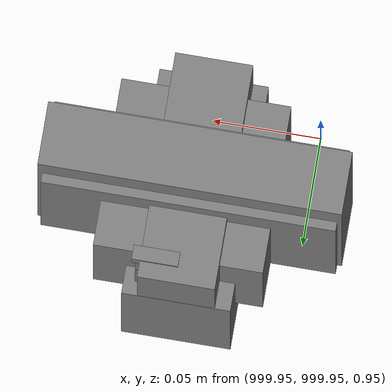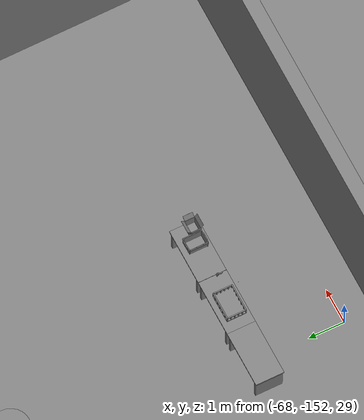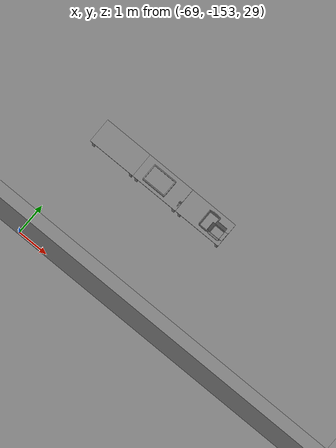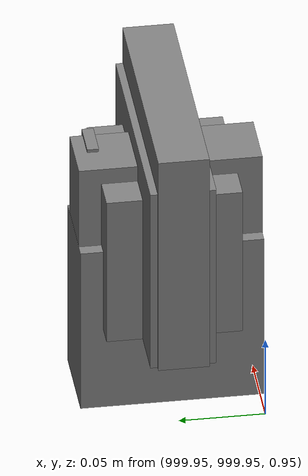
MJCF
<mujoco>
    <option gravity="0.000000000 0.000000000 -9.810000420" timestep="0.0049999999" integrator="implicitfast" density="1.225" viscosity="1.8000001e-05" noslip_iterations="10" iterations="100" sdf_iterations="50">
        <flag multiccd="disable"/>
    </option>
    <size memory="1000M"/>
    <compiler coordinate="local"/>
    <worldbody>
        <light cutoff="30" pos="0 1 1" dir="0 -1 -2"/>
        <light cutoff="30" pos="0 -1 1" dir="0 1 -2"/>
        <body pos="-64.866622925 -149.383972168 30.183746338" euler="89.999984741 89.999946594 0.000000000" name="openloong_gripper_2f85_fix_base_usda_bluebox_01">
            <geom contype="1" conaffinity="1" density="1000" type="box" material="" rgba="0.500000000 0.500000000 0.500000000 1.000000000" solimp="0.899999976 0.949999988 0.001000000" friction="1.000000000 0.005000000 0.000100000" solref="0.020000000 1.000000000" margin="0" condim="3" group="0" pos="0.276580811 0.187225342 0.000068665" quat="0.707106948 0.000077471 0.707106352 0.000077486" size="0.100000001 0.057999998 0.010000000" name="openloong_gripper_2f85_fix_base_usda_geom_371E0E9D_4AE3_4EA4_B1A5_58400002444A"/>
            <geom contype="1" conaffinity="1" density="1000" type="box" material="" rgba="0.500000000 0.500000000 0.500000000 1.000000000" solimp="0.899999976 0.949999988 0.001000000" friction="1.000000000 0.005000000 0.000100000" solref="0.020000000 1.000000000" margin="0" condim="3" group="0" pos="0.000000000 0.002883911 0.000000000" quat="0.999999881 0.000000000 0.000000000 0.000000000" size="0.254000008 0.003000000 0.172000006" name="openloong_gripper_2f85_fix_base_usda_geom_1DA88A1A_951F_48E3_8275_2108E54223BF"/>
            <geom contype="1" conaffinity="1" density="1000" type="box" material="" rgba="0.500000000 0.500000000 0.500000000 1.000000000" solimp="0.899999976 0.949999988 0.001000000" friction="1.000000000 0.005000000 0.000100000" solref="0.020000000 1.000000000" margin="0" condim="3" group="0" pos="0.000000000 0.124874115 0.173484802" quat="0.999796331 0.020176515 -0.000000015 0.000000030" size="0.259999990 0.119999997 0.007000000" name="openloong_gripper_2f85_fix_base_usda_geom_C52622EB_A684_4655_961D_9010D4B02073"/>
            <geom contype="1" conaffinity="1" density="1000" type="box" material="" rgba="0.500000000 0.500000000 0.500000000 1.000000000" solimp="0.899999976 0.949999988 0.001000000" friction="1.000000000 0.005000000 0.000100000" solref="0.020000000 1.000000000" margin="0" condim="3" group="0" pos="0.000000000 0.124874115 -0.173469543" quat="0.999796331 -0.020176545 -0.000000015 0.000000000" size="0.259999990 0.119999997 0.007000000" name="openloong_gripper_2f85_fix_base_usda_geom_FB94422F_ECD1_4D59_A321_784DE97A2B1D"/>
            <geom contype="1" conaffinity="1" density="1000" type="box" material="" rgba="0.500000000 0.500000000 0.500000000 1.000000000" solimp="0.899999976 0.949999988 0.001000000" friction="1.000000000 0.005000000 0.000100000" solref="0.020000000 1.000000000" margin="0" condim="3" group="0" pos="0.000000000 0.214008331 0.188980103" quat="0.999912977 0.013176724 0.000000015 0.000000000" size="0.259999990 0.029999999 0.012500000" name="openloong_gripper_2f85_fix_base_usda_geom_1961BA4D_F7A3_4EC7_BBAE_E247D3D47030"/>
            <geom contype="1" conaffinity="1" density="1000" type="box" material="" rgba="0.500000000 0.500000000 0.500000000 1.000000000" solimp="0.899999976 0.949999988 0.001000000" friction="1.000000000 0.005000000 0.000100000" solref="0.020000000 1.000000000" margin="0" condim="3" group="0" pos="-0.258361816 0.125289917 0.001876831" quat="0.702796936 -0.020792112 0.710783124 0.020769298" size="0.189999998 0.119999997 0.009000000" name="openloong_gripper_2f85_fix_base_usda_geom_A2280032_C747_4C97_A80C_69A999FA09E1"/>
            <geom contype="1" conaffinity="1" density="1000" type="box" material="" rgba="0.500000000 0.500000000 0.500000000 1.000000000" solimp="0.899999976 0.949999988 0.001000000" friction="1.000000000 0.005000000 0.000100000" solref="0.020000000 1.000000000" margin="0" condim="3" group="0" pos="0.000000000 0.214008331 -0.188980103" quat="0.999912977 -0.013176769 0.000000030 0.000000015" size="0.259999990 0.029999999 0.012500000" name="openloong_gripper_2f85_fix_base_usda_geom_01EB59A5_726C_4364_8931_5A376A5F04F8"/>
            <geom contype="1" conaffinity="1" density="1000" type="box" material="" rgba="0.500000000 0.500000000 0.500000000 1.000000000" solimp="0.899999976 0.949999988 0.001000000" friction="1.000000000 0.005000000 0.000100000" solref="0.020000000 1.000000000" margin="0" condim="3" group="0" pos="-0.276611328 0.187225342 0.000068665" quat="0.707106650 0.000077441 0.707106709 0.000077456" size="0.100000001 0.057999998 0.010000000" name="openloong_gripper_2f85_fix_base_usda_geom_A5ED6DFF_6430_4434_AFCB_905767FA25BF"/>
            <geom contype="1" conaffinity="1" density="1000" type="box" material="" rgba="0.500000000 0.500000000 0.500000000 1.000000000" solimp="0.899999976 0.949999988 0.001000000" friction="1.000000000 0.005000000 0.000100000" solref="0.020000000 1.000000000" margin="0" condim="3" group="0" pos="0.258331299 0.125289917 0.001876831" quat="0.702851415 0.018856421 0.710823774 -0.019329369" size="0.189999998 0.119999997 0.009000000" name="openloong_gripper_2f85_fix_base_usda_geom_EEC46349_4F67_46C7_8602_74B4412F46FF"/>
            <freejoint name="openloong_gripper_2f85_fix_base_usda_bluebox_01_joint"/>
            <site size="0.005000000 0.005000000 0.005000000" rgba="0.500000000 0.500000000 0.500000000 1.000000000" pos="0.000000000 0.000000000 0.000000000" quat="0.999961913 0.008726534 0.000000000 0.000000000" group="0" type="sphere" name="openloong_gripper_2f85_fix_base_usda_bluebox_01site"/>
        </body>
        <body pos="-64.496299744 -149.491867065 30.235729218" euler="0.000000000 0.000000000 89.999946594" name="openloong_gripper_2f85_fix_base_usda_cardboardbox_01">
            <geom contype="1" conaffinity="1" density="1000" type="box" material="" rgba="0.500000000 0.500000000 0.500000000 1.000000000" solimp="0.899999976 0.949999988 0.001000000" friction="1.000000000 0.005000000 0.000100000" solref="0.020000000 1.000000000" margin="0" condim="3" group="0" pos="-0.003166199 -0.004086494 0.005052090" quat="1.000000000 0.000000000 0.000000000 0.000000000" size="0.142499998 0.177500010 0.005000000" name="openloong_gripper_2f85_fix_base_usda_geom_8C9CD6F8_07FA_45E1_8481_54B43EB2D732"/>
            <geom contype="1" conaffinity="1" density="1000" type="box" material="" rgba="0.500000000 0.500000000 0.500000000 1.000000000" solimp="0.899999976 0.949999988 0.001000000" friction="1.000000000 0.005000000 0.000100000" solref="0.020000000 1.000000000" margin="0" condim="3" group="0" pos="-0.003166199 0.170316696 0.150570869" quat="1.000000000 0.000000000 0.000000000 0.000000000" size="0.142499998 0.005000000 0.149999991" name="openloong_gripper_2f85_fix_base_usda_geom_27F6CACF_81FC_44CF_9C5A_4226137ACEA6"/>
            <geom contype="1" conaffinity="1" density="1000" type="box" material="" rgba="0.500000000 0.500000000 0.500000000 1.000000000" solimp="0.899999976 0.949999988 0.001000000" friction="1.000000000 0.005000000 0.000100000" solref="0.020000000 1.000000000" margin="0" condim="3" group="0" pos="-0.147399902 -0.005307198 0.150570869" quat="1.000000000 0.000000000 0.000000000 0.000000000" size="0.005000000 0.177500010 0.149999991" name="openloong_gripper_2f85_fix_base_usda_geom_625015C9_826B_4CFE_A9A6_E4DF4F5D5653"/>
            <geom contype="1" conaffinity="1" density="1000" type="box" material="" rgba="0.500000000 0.500000000 0.500000000 1.000000000" solimp="0.899999976 0.949999988 0.001000000" friction="1.000000000 0.005000000 0.000100000" solref="0.020000000 1.000000000" margin="0" condim="3" group="0" pos="0.140275955 -0.005307198 0.150570869" quat="1.000000000 0.000000000 0.000000000 0.000000000" size="0.005000000 0.177500010 0.149999991" name="openloong_gripper_2f85_fix_base_usda_geom_20342AD1_872C_43E8_ACEE_01860BE9634B"/>
            <geom contype="1" conaffinity="1" density="1000" type="box" material="" rgba="0.500000000 0.500000000 0.500000000 1.000000000" solimp="0.899999976 0.949999988 0.001000000" friction="1.000000000 0.005000000 0.000100000" solref="0.020000000 1.000000000" margin="0" condim="3" group="0" pos="-0.003166199 -0.181550980 0.150570869" quat="1.000000000 0.000000000 0.000000000 0.000000000" size="0.142499998 0.005000000 0.149999991" name="openloong_gripper_2f85_fix_base_usda_geom_42600CA6_4D5E_4EE2_A3F7_241072876272"/>
            <freejoint name="openloong_gripper_2f85_fix_base_usda_cardboardbox_01_joint"/>
            <site size="0.005000000 0.005000000 0.005000000" rgba="0.500000000 0.500000000 0.500000000 1.000000000" pos="0.000000000 0.000000000 0.000000000" quat="0.999961913 0.008726535 0.000000000 0.000000000" group="0" type="sphere" name="openloong_gripper_2f85_fix_base_usda_site_86D97FA6_6ED6_4AAA_A62A_31718DD200B3"/>
            <body pos="0.139160156 -0.004048347 0.301930904" euler="-179.999954224 49.383502960 179.999954224" name="openloong_gripper_2f85_fix_base_usda_A1_006">
                <geom contype="1" conaffinity="1" density="1000" type="box" material="" rgba="0.500000000 0.500000000 0.500000000 1.000000000" solimp="0.899999976 0.949999988 0.001000000" friction="1.000000000 0.005000000 0.000100000" solref="0.020000000 1.000000000" margin="0" condim="3" group="0" pos="-0.071587563 0.000009537 0.001745224" quat="0.999999881 0.000000000 0.000000000 0.000000000" size="0.071249999 0.179999992 0.002500000" name="openloong_gripper_2f85_fix_base_usda_geom_0D066BBE_FE68_4AB7_9D08_DC040A1BCB2F"/>
                <joint armature="0" stiffness="0.07" damping="0.0099999998" axis="0.000000 1.000000 0.000000" type="hinge" name="openloong_gripper_2f85_fix_base_usda_A1_006"/>
            </body>
            <body pos="-0.145902634 -0.004086494 0.301938057" euler="-180.000000000 -60.000011444 -180.000000000" name="openloong_gripper_2f85_fix_base_usda_A2_006">
                <geom contype="1" conaffinity="1" density="1000" type="box" material="" rgba="0.500000000 0.500000000 0.500000000 1.000000000" solimp="0.899999976 0.949999988 0.001000000" friction="1.000000000 0.005000000 0.000100000" solref="0.020000000 1.000000000" margin="0" condim="3" group="0" pos="0.071268082 0.000009537 0.002717972" quat="0.000002921 0.000000000 -0.000000030 0.999999881" size="0.071249999 0.179999992 0.002500000" name="openloong_gripper_2f85_fix_base_usda_geom_E96620EE_FA73_476F_A8F8_AFE409EE2D39"/>
                <joint armature="0" stiffness="0.07" damping="0.0099999998" axis="0.000000 1.000000 0.000000" type="hinge" name="openloong_gripper_2f85_fix_base_usda_A2_006"/>
            </body>
            <body pos="-0.003385544 0.175991058 0.301930904" euler="-125.858116150 -0.000004561 0.000002331" name="openloong_gripper_2f85_fix_base_usda_B2_006">
                <geom contype="1" conaffinity="1" density="1000" type="box" material="" rgba="0.500000000 0.500000000 0.500000000 1.000000000" solimp="0.899999976 0.949999988 0.001000000" friction="1.000000000 0.005000000 0.000100000" solref="0.020000000 1.000000000" margin="0" condim="3" group="0" pos="0.000009537 -0.070939064 -0.002470016" quat="0.999614120 0.027776197 -0.000000015 0.000000030" size="0.137500003 0.064999998 0.005000000" name="openloong_gripper_2f85_fix_base_usda_geom_0166F89F_1070_4CB6_A5A5_19F86759A54A"/>
                <joint armature="0" stiffness="0.07" damping="0.0099999998" axis="1.000000 0.000000 0.000000" type="hinge" name="openloong_gripper_2f85_fix_base_usda_B2_006"/>
            </body>
            <body pos="-0.003385544 -0.184140205 0.301938057" euler="147.805557251 0.000000000 0.000000000" name="openloong_gripper_2f85_fix_base_usda_B1_006">
                <geom contype="1" conaffinity="1" density="1000" type="box" material="" rgba="0.500000000 0.500000000 0.500000000 1.000000000" solimp="0.899999976 0.949999988 0.001000000" friction="1.000000000 0.005000000 0.000100000" solref="0.020000000 1.000000000" margin="0" condim="3" group="0" pos="-0.000028610 0.070202351 -0.002703667" quat="0.999614179 -0.027776167 0.000000000 0.000000000" size="0.137500003 0.064999998 0.005000000" name="openloong_gripper_2f85_fix_base_usda_geom_65E44CB3_1642_4318_933F_D8EA196F4161"/>
                <joint armature="0" stiffness="0.07" damping="0.0099999998" axis="1.000000 0.000000 0.000000" type="hinge" name="openloong_gripper_2f85_fix_base_usda_B1_006"/>
            </body>
        </body>
        <body pos="-65.882858276 -149.481979370 30.229999542" euler="-64.487716675 0.000000000 0.000000000" name="openloong_gripper_2f85_fix_base_usda_Barcode">
            <geom contype="1" conaffinity="1" density="1000" type="box" material="" rgba="0.500000000 0.500000000 0.500000000 1.000000000" solimp="0.899999976 0.949999988 0.001000000" friction="1.000000000 0.005000000 0.000100000" solref="0.020000000 1.000000000" margin="0" condim="3" group="0" pos="0.000000000 0.013038635 0.001419067" quat="0.000000000 0.000000000 0.000000000 1.000000119" size="0.034000002 0.010000000 0.017999999" name="openloong_gripper_2f85_fix_base_usda_geom_F66B7134_168F_4395_92E2_A298E99FF288"/>
            <geom contype="1" conaffinity="1" density="1000" type="box" material="" rgba="0.500000000 0.500000000 0.500000000 1.000000000" solimp="0.899999976 0.949999988 0.001000000" friction="1.000000000 0.005000000 0.000100000" solref="0.020000000 1.000000000" margin="0" condim="3" group="0" pos="0.000000000 -0.035301208 -0.007095337" quat="0.000000000 0.000000000 -0.043619365 0.999048233" size="0.028999999 0.010000000 0.020000000" name="openloong_gripper_2f85_fix_base_usda_geom_CB14B7DA_17BB_457D_AEAA_5AB58531EF44"/>
            <geom contype="1" conaffinity="1" density="1000" type="box" material="" rgba="0.500000000 0.500000000 0.500000000 1.000000000" solimp="0.899999976 0.949999988 0.001000000" friction="1.000000000 0.005000000 0.000100000" solref="0.020000000 1.000000000" margin="0" condim="3" group="0" pos="0.000000000 -0.043411255 -0.011749268" quat="0.922262907 0.386563420 0.000000000 0.000000000" size="0.026000001 0.010000000 0.020000000" name="openloong_gripper_2f85_fix_base_usda_geom_CB0E065C_7B7E_4494_955D_11A2691D1283"/>
            <geom contype="1" conaffinity="1" density="1000" type="box" material="" rgba="0.500000000 0.500000000 0.500000000 1.000000000" solimp="0.899999976 0.949999988 0.001000000" friction="1.000000000 0.005000000 0.000100000" solref="0.020000000 1.000000000" margin="0" condim="3" group="0" pos="0.000000000 -0.016967773 -0.031860352" quat="0.000000000 0.000000000 0.000000000 1.000000119" size="0.008000000 0.010000000 0.013000000" name="openloong_gripper_2f85_fix_base_usda_geom_A35E399C_07C9_44A2_B2A5_81252810AA71"/>
            <geom contype="1" conaffinity="1" density="1000" type="box" material="" rgba="0.500000000 0.500000000 0.500000000 1.000000000" solimp="0.899999976 0.949999988 0.001000000" friction="1.000000000 0.005000000 0.000100000" solref="0.020000000 1.000000000" margin="0" condim="3" group="0" pos="0.000000000 -0.001869202 0.000312805" quat="0.953716993 0.300705761 0.000000000 0.000000000" size="0.032000002 0.010000000 0.018999999" name="openloong_gripper_2f85_fix_base_usda_geom_6CCAAD58_94F6_4606_ACB3_B0556F2551DD"/>
            <geom contype="1" conaffinity="1" density="1000" type="box" material="" rgba="0.500000000 0.500000000 0.500000000 1.000000000" solimp="0.899999976 0.949999988 0.001000000" friction="1.000000000 0.005000000 0.000100000" solref="0.020000000 1.000000000" margin="0" condim="3" group="0" pos="0.000000000 -0.019531250 -0.003173828" quat="0.953716993 0.300705761 0.000000000 0.000000000" size="0.030999999 0.010000000 0.020000000" name="openloong_gripper_2f85_fix_base_usda_geom_FD7B8DB6_189E_4807_B737_7E998BDF7F85"/>
            <geom contype="1" conaffinity="1" density="1000" type="box" material="" rgba="0.500000000 0.500000000 0.500000000 1.000000000" solimp="0.899999976 0.949999988 0.001000000" friction="1.000000000 0.005000000 0.000100000" solref="0.020000000 1.000000000" margin="0" condim="3" group="0" pos="0.000000000 -0.035301208 -0.007095337" quat="0.953716993 0.300705761 0.000000000 0.000000000" size="0.028999999 0.010000000 0.020000000" name="openloong_gripper_2f85_fix_base_usda_geom_E3DD1A11_2559_4AB5_818E_DA13E0490FE3"/>
            <geom contype="1" conaffinity="1" density="1000" type="box" material="" rgba="0.500000000 0.500000000 0.500000000 1.000000000" solimp="0.899999976 0.949999988 0.001000000" friction="1.000000000 0.005000000 0.000100000" solref="0.020000000 1.000000000" margin="0" condim="3" group="0" pos="0.000000000 -0.042617798 -0.071121216" quat="0.000000000 0.000000000 0.000000000 1.000000119" size="0.013000000 0.021000000 0.059999999" name="openloong_gripper_2f85_fix_base_usda_geom_9CDC839F_829D_4B48_9ED7_FA3369757EBE"/>
            <freejoint name="openloong_gripper_2f85_fix_base_usda_Barcode_joint"/>
            <site size="0.005000000 0.005000000 0.005000000" rgba="0.500000000 0.500000000 0.500000000 1.000000000" pos="0.000000000 0.000000000 0.000000000" quat="1.000000000 0.000000000 0.000000000 0.000000000" group="0" type="sphere" name="openloong_gripper_2f85_fix_base_usda_Barcode_site"/>
        </body>
        <body pos="-66.745018005 -149.392349243 30.184000015" euler="0.000000000 0.000000000 89.999946594" name="[22330691125568]_Basket_01">
            <geom contype="1" conaffinity="1" density="1000" type="box" material="" rgba="0.500000000 0.500000000 0.500000000 1.000000000" solimp="0.899999976 0.949999988 0.001000000" friction="1.000000000 0.005000000 0.000100000" solref="0.020000000 1.000000000" margin="0" condim="3" group="0" pos="-0.052425385 0.389207840 0.089787483" quat="0.707107008 0.000000000 0.000000000 0.707106411" size="0.014249999 0.014249999 0.059999999" name="[22330691125568]_geom_C9F04EFB_A2DA_4BD5_89E9_50597288B5D9"/>
            <geom contype="1" conaffinity="1" density="1000" type="box" material="" rgba="0.500000000 0.500000000 0.500000000 1.000000000" solimp="0.899999976 0.949999988 0.001000000" friction="1.000000000 0.005000000 0.000100000" solref="0.020000000 1.000000000" margin="0" condim="3" group="0" pos="0.264015198 -0.133043289 0.089787483" quat="0.707107008 0.000000000 0.000000000 0.707106411" size="0.014249999 0.014249999 0.059999999" name="[22330691125568]_geom_49FC9183_9967_44E6_8C75_51814C8E4160"/>
            <geom contype="1" conaffinity="1" density="1000" type="box" material="" rgba="0.500000000 0.500000000 0.500000000 1.000000000" solimp="0.899999976 0.949999988 0.001000000" friction="1.000000000 0.005000000 0.000100000" solref="0.020000000 1.000000000" margin="0" condim="3" group="0" pos="-0.264015198 -0.265548706 0.089793205" quat="0.707107008 0.000000000 0.000000000 0.707106411" size="0.014249999 0.014249999 0.059999999" name="[22330691125568]_geom_2D7772C4_9206_4374_B188_0D82BE7A69E4"/>
            <geom contype="1" conaffinity="1" density="1000" type="box" material="" rgba="0.500000000 0.500000000 0.500000000 1.000000000" solimp="0.899999976 0.949999988 0.001000000" friction="1.000000000 0.005000000 0.000100000" solref="0.020000000 1.000000000" margin="0" condim="3" group="0" pos="-0.160263062 -0.389322281 0.089793205" quat="0.707107008 0.000000000 0.000000000 0.707106411" size="0.014249999 0.014249999 0.059999999" name="[22330691125568]_geom_F1F7F35F_5E44_4545_97B5_04FDA73FB401"/>
            <geom contype="1" conaffinity="1" density="1000" type="box" material="" rgba="0.500000000 0.500000000 0.500000000 1.000000000" solimp="0.899999976 0.949999988 0.001000000" friction="1.000000000 0.005000000 0.000100000" solref="0.020000000 1.000000000" margin="0" condim="3" group="0" pos="0.162265778 -0.389322281 0.089787483" quat="0.707107008 0.000000000 0.000000000 0.707106411" size="0.014249999 0.014249999 0.059999999" name="[22330691125568]_geom_E466A709_987D_458E_9C9C_EAA2EA150834"/>
            <geom contype="1" conaffinity="1" density="1000" type="box" material="" rgba="0.500000000 0.500000000 0.500000000 1.000000000" solimp="0.899999976 0.949999988 0.001000000" friction="1.000000000 0.005000000 0.000100000" solref="0.020000000 1.000000000" margin="0" condim="3" group="0" pos="0.264015198 0.389207840 0.089787483" quat="0.707107008 0.000000000 0.000000000 0.707106411" size="0.014249999 0.014249999 0.059999999" name="[22330691125568]_geom_57680E8E_E71F_4AE0_B409_383B864392B3"/>
            <geom contype="1" conaffinity="1" density="1000" type="box" material="" rgba="0.500000000 0.500000000 0.500000000 1.000000000" solimp="0.899999976 0.949999988 0.001000000" friction="1.000000000 0.005000000 0.000100000" solref="0.020000000 1.000000000" margin="0" condim="3" group="0" pos="-0.264015198 -0.133043289 0.089793205" quat="0.707107008 0.000000000 0.000000000 0.707106411" size="0.014249999 0.014249999 0.059999999" name="[22330691125568]_geom_D15684E4_B9A3_438C_8002_A7E1CD128B4C"/>
            <geom contype="1" conaffinity="1" density="1000" type="box" material="" rgba="0.500000000 0.500000000 0.500000000 1.000000000" solimp="0.899999976 0.949999988 0.001000000" friction="1.000000000 0.005000000 0.000100000" solref="0.020000000 1.000000000" margin="0" condim="3" group="0" pos="-0.264026642 0.269256592 0.089793205" quat="0.707107008 0.000000000 0.000000000 0.707106411" size="0.014249999 0.014249999 0.059999999" name="[22330691125568]_geom_C6C65403_A781_49D2_A721_BDEEA4F4F6FB"/>
            <geom contype="1" conaffinity="1" density="1000" type="box" material="" rgba="0.500000000 0.500000000 0.500000000 1.000000000" solimp="0.899999976 0.949999988 0.001000000" friction="1.000000000 0.005000000 0.000100000" solref="0.020000000 1.000000000" margin="0" condim="3" group="0" pos="0.054462433 0.389207840 0.089787483" quat="0.707107008 0.000000000 0.000000000 0.707106411" size="0.014249999 0.014249999 0.059999999" name="[22330691125568]_geom_17E72E1C_CE85_4D18_A0E2_5427BB25046C"/>
            <geom contype="1" conaffinity="1" density="1000" type="box" material="" rgba="0.500000000 0.500000000 0.500000000 1.000000000" solimp="0.899999976 0.949999988 0.001000000" friction="1.000000000 0.005000000 0.000100000" solref="0.020000000 1.000000000" margin="0" condim="3" group="0" pos="0.054462433 -0.389322281 0.089787483" quat="0.707107008 0.000000000 0.000000000 0.707106411" size="0.014249999 0.014249999 0.059999999" name="[22330691125568]_geom_2FC20D89_E95E_482F_9D59_321FB97220F5"/>
            <geom contype="1" conaffinity="1" density="1000" type="box" material="" rgba="0.500000000 0.500000000 0.500000000 1.000000000" solimp="0.899999976 0.949999988 0.001000000" friction="1.000000000 0.005000000 0.000100000" solref="0.020000000 1.000000000" margin="0" condim="3" group="0" pos="0.264015198 0.269256592 0.089793205" quat="0.707107008 0.000000000 0.000000000 0.707106411" size="0.014249999 0.014249999 0.059999999" name="[22330691125568]_geom_5E9986BE_0E9E_47EC_B774_364ABD847D9C"/>
            <geom contype="1" conaffinity="1" density="1000" type="box" material="" rgba="0.500000000 0.500000000 0.500000000 1.000000000" solimp="0.899999976 0.949999988 0.001000000" friction="1.000000000 0.005000000 0.000100000" solref="0.020000000 1.000000000" margin="0" condim="3" group="0" pos="0.264015198 -0.389322281 0.089787483" quat="0.707107008 0.000000000 0.000000000 0.707106411" size="0.014249999 0.014249999 0.059999999" name="[22330691125568]_geom_25122209_38FD_48E9_B7B8_7E4F62A468EA"/>
            <geom contype="1" conaffinity="1" density="1000" type="box" material="" rgba="0.500000000 0.500000000 0.500000000 1.000000000" solimp="0.899999976 0.949999988 0.001000000" friction="1.000000000 0.005000000 0.000100000" solref="0.020000000 1.000000000" margin="0" condim="3" group="0" pos="0.000000000 0.000000000 0.015998840" quat="0.707107008 0.000000000 0.000000000 0.707106411" size="0.403499991 0.279000014 0.015750000" name="[22330691125568]_geom_ADDE0D7F_066A_4D78_9C57_BFB9DE859464"/>
            <geom contype="1" conaffinity="1" density="1000" type="box" material="" rgba="0.500000000 0.500000000 0.500000000 1.000000000" solimp="0.899999976 0.949999988 0.001000000" friction="1.000000000 0.005000000 0.000100000" solref="0.020000000 1.000000000" margin="0" condim="3" group="0" pos="0.000000000 -0.389476776 0.163619041" quat="0.707107008 0.000000000 0.000000000 0.707106411" size="0.015000000 0.277500004 0.015750000" name="[22330691125568]_geom_3D8C2BC2_4C0D_4593_88A2_A1E9E549AB45"/>
            <geom contype="1" conaffinity="1" density="1000" type="box" material="" rgba="0.500000000 0.500000000 0.500000000 1.000000000" solimp="0.899999976 0.949999988 0.001000000" friction="1.000000000 0.005000000 0.000100000" solref="0.020000000 1.000000000" margin="0" condim="3" group="0" pos="0.162265778 0.389207840 0.089787483" quat="0.707107008 0.000000000 0.000000000 0.707106411" size="0.014249999 0.014249999 0.059999999" name="[22330691125568]_geom_E1BD2573_3BE5_4470_915D_5152F6A8AEBF"/>
            <geom contype="1" conaffinity="1" density="1000" type="box" material="" rgba="0.500000000 0.500000000 0.500000000 1.000000000" solimp="0.899999976 0.949999988 0.001000000" friction="1.000000000 0.005000000 0.000100000" solref="0.020000000 1.000000000" margin="0" condim="3" group="0" pos="0.000000000 0.389471054 0.163619041" quat="0.707107008 0.000000000 0.000000000 0.707106411" size="0.015000000 0.277500004 0.015750000" name="[22330691125568]_geom_3B5E66FF_AF16_4875_83A1_1BA8B77DDE82"/>
            <geom contype="1" conaffinity="1" density="1000" type="box" material="" rgba="0.500000000 0.500000000 0.500000000 1.000000000" solimp="0.899999976 0.949999988 0.001000000" friction="1.000000000 0.005000000 0.000100000" solref="0.020000000 1.000000000" margin="0" condim="3" group="0" pos="-0.263511658 0.000000000 0.163619041" quat="0.707107008 0.000000000 0.000000000 0.707106411" size="0.403499991 0.015000000 0.015750000" name="[22330691125568]_geom_383821C6_83DE_4030_9655_77498C6B94A4"/>
            <geom contype="1" conaffinity="1" density="1000" type="box" material="" rgba="0.500000000 0.500000000 0.500000000 1.000000000" solimp="0.899999976 0.949999988 0.001000000" friction="1.000000000 0.005000000 0.000100000" solref="0.020000000 1.000000000" margin="0" condim="3" group="0" pos="-0.264015198 0.141334534 0.089793205" quat="0.707107008 0.000000000 0.000000000 0.707106411" size="0.014249999 0.014249999 0.059999999" name="[22330691125568]_geom_B90F606D_28F1_4B15_8EC0_3696F96A4482"/>
            <geom contype="1" conaffinity="1" density="1000" type="box" material="" rgba="0.500000000 0.500000000 0.500000000 1.000000000" solimp="0.899999976 0.949999988 0.001000000" friction="1.000000000 0.005000000 0.000100000" solref="0.020000000 1.000000000" margin="0" condim="3" group="0" pos="0.264015198 -0.265548706 0.089787483" quat="0.707107008 0.000000000 0.000000000 0.707106411" size="0.014249999 0.014249999 0.059999999" name="[22330691125568]_geom_328BA002_6F0E_4200_9B14_3B23F069CF6B"/>
            <geom contype="1" conaffinity="1" density="1000" type="box" material="" rgba="0.500000000 0.500000000 0.500000000 1.000000000" solimp="0.899999976 0.949999988 0.001000000" friction="1.000000000 0.005000000 0.000100000" solref="0.020000000 1.000000000" margin="0" condim="3" group="0" pos="-0.160263062 0.389207840 0.089787483" quat="0.707107008 0.000000000 0.000000000 0.707106411" size="0.014249999 0.014249999 0.059999999" name="[22330691125568]_geom_774F5C00_FE6B_4E02_BC21_7D557A1D2F5C"/>
            <geom contype="1" conaffinity="1" density="1000" type="box" material="" rgba="0.500000000 0.500000000 0.500000000 1.000000000" solimp="0.899999976 0.949999988 0.001000000" friction="1.000000000 0.005000000 0.000100000" solref="0.020000000 1.000000000" margin="0" condim="3" group="0" pos="-0.052425385 -0.389322281 0.089787483" quat="0.707107008 0.000000000 0.000000000 0.707106411" size="0.014249999 0.014249999 0.059999999" name="[22330691125568]_geom_2BA25F52_BA13_4BDF_80CF_091313E53B0C"/>
            <geom contype="1" conaffinity="1" density="1000" type="box" material="" rgba="0.500000000 0.500000000 0.500000000 1.000000000" solimp="0.899999976 0.949999988 0.001000000" friction="1.000000000 0.005000000 0.000100000" solref="0.020000000 1.000000000" margin="0" condim="3" group="0" pos="-0.264026642 -0.389322281 0.089793205" quat="0.707107008 0.000000000 0.000000000 0.707106411" size="0.014249999 0.014249999 0.059999999" name="[22330691125568]_geom_138F9628_B3FE_4F1D_BC20_2969BEEEB992"/>
            <geom contype="1" conaffinity="1" density="1000" type="box" material="" rgba="0.500000000 0.500000000 0.500000000 1.000000000" solimp="0.899999976 0.949999988 0.001000000" friction="1.000000000 0.005000000 0.000100000" solref="0.020000000 1.000000000" margin="0" condim="3" group="0" pos="0.264015198 0.141334534 0.089787483" quat="0.707107008 0.000000000 0.000000000 0.707106411" size="0.014249999 0.014249999 0.059999999" name="[22330691125568]_geom_AF1819B7_211A_44B1_9D82_AFDC090B8463"/>
            <geom contype="1" conaffinity="1" density="1000" type="box" material="" rgba="0.500000000 0.500000000 0.500000000 1.000000000" solimp="0.899999976 0.949999988 0.001000000" friction="1.000000000 0.005000000 0.000100000" solref="0.020000000 1.000000000" margin="0" condim="3" group="0" pos="-0.264015198 0.389207840 0.089793205" quat="0.707107008 0.000000000 0.000000000 0.707106411" size="0.014249999 0.014249999 0.059999999" name="[22330691125568]_geom_995839F9_63C3_4BDD_AF72_079D45D57B77"/>
            <geom contype="1" conaffinity="1" density="1000" type="box" material="" rgba="0.500000000 0.500000000 0.500000000 1.000000000" solimp="0.899999976 0.949999988 0.001000000" friction="1.000000000 0.005000000 0.000100000" solref="0.020000000 1.000000000" margin="0" condim="3" group="0" pos="0.264015198 0.004480362 0.089787483" quat="0.707107008 0.000000000 0.000000000 0.707106411" size="0.014249999 0.014249999 0.059999999" name="[22330691125568]_geom_3609F3E4_F143_4C1D_BB62_828EF0B204BE"/>
            <geom contype="1" conaffinity="1" density="1000" type="box" material="" rgba="0.500000000 0.500000000 0.500000000 1.000000000" solimp="0.899999976 0.949999988 0.001000000" friction="1.000000000 0.005000000 0.000100000" solref="0.020000000 1.000000000" margin="0" condim="3" group="0" pos="0.263694763 -0.000011444 0.163619041" quat="0.707107008 0.000000000 0.000000000 0.707106411" size="0.403499991 0.015000000 0.015750000" name="[22330691125568]_geom_D5102C1B_C3ED_4E2F_A924_987A31288FC2"/>
            <geom contype="1" conaffinity="1" density="1000" type="box" material="" rgba="0.500000000 0.500000000 0.500000000 1.000000000" solimp="0.899999976 0.949999988 0.001000000" friction="1.000000000 0.005000000 0.000100000" solref="0.020000000 1.000000000" margin="0" condim="3" group="0" pos="-0.264015198 0.004480362 0.089793205" quat="0.707107008 0.000000000 0.000000000 0.707106411" size="0.014249999 0.014249999 0.059999999" name="[22330691125568]_geom_B9EE5D0B_1E2B_477D_AB7A_5E6FAFCE50D1"/>
            <freejoint name="[22330691125568]_joint_8D0C78F2_E7BA_4856_994C_6B471265C348"/>
        </body>
        <body pos="0.000000000 0.000000000 0.000000000" euler="0.000000000 0.000000000 0.000000000" name="Static Objects_Static Objects">
            <geom contype="1" conaffinity="1" density="1000" type="box" material="" rgba="0.500000000 0.500000000 0.500000000 1.000000000" solimp="0.899999976 0.949999988 0.001000000" friction="1.000000000 0.005000000 0.000100000" solref="0.020000000 1.000000000" margin="0" condim="3" group="0" pos="-67.544113159 -149.365814209 29.727830887" quat="0.500000417 0.499999970 0.499999553 0.499999970" size="0.381000012 0.319999993 0.041000001" name="Static Objects_geom_B035E69C_C837_4638_8FC3_2B82D00BE70E"/>
            <geom contype="1" conaffinity="1" density="1000" type="box" material="" rgba="0.500000000 0.500000000 0.500000000 1.000000000" solimp="0.899999976 0.949999988 0.001000000" friction="1.000000000 0.005000000 0.000100000" solref="0.020000000 1.000000000" margin="0" condim="3" group="0" pos="-68.239501953 -149.365814209 30.086868286" quat="0.500000417 0.499999970 0.499999553 0.499999970" size="0.370999992 0.039500002 0.745000005" name="Static Objects_geom_4F625052_FEAB_4A92_BA99_5543E9AF3678"/>
            <geom contype="1" conaffinity="1" density="1000" type="box" material="" rgba="0.500000000 0.500000000 0.500000000 1.000000000" solimp="0.899999976 0.949999988 0.001000000" friction="1.000000000 0.005000000 0.000100000" solref="0.020000000 1.000000000" margin="0" condim="3" group="0" pos="-68.239501953 -149.365814209 30.147235870" quat="0.500000417 0.499999970 0.499999553 0.499999970" size="0.400000006 0.022000000 0.800000012" name="Static Objects_geom_82E3605A_14CE_4115_8AF5_B051A227E9E4"/>
            <geom contype="1" conaffinity="1" density="1000" type="box" material="" rgba="0.500000000 0.500000000 0.500000000 1.000000000" solimp="0.899999976 0.949999988 0.001000000" friction="1.000000000 0.005000000 0.000100000" solref="0.020000000 1.000000000" margin="0" condim="3" group="0" pos="-68.934890747 -149.365814209 29.727830887" quat="0.500000417 0.499999970 0.499999553 0.499999970" size="0.381000012 0.319999993 0.041000001" name="Static Objects_geom_9778AC3E_8C7E_4F74_AF71_F5E3983094F1"/>
            <geom contype="1" conaffinity="1" density="1000" type="box" material="" rgba="0.500000000 0.500000000 0.500000000 1.000000000" solimp="0.899999976 0.949999988 0.001000000" friction="1.000000000 0.005000000 0.000100000" solref="0.020000000 1.000000000" margin="0" condim="3" group="0" pos="-68.239501953 -149.365814209 29.561563492" quat="0.500000417 0.499999970 0.499999553 0.499999970" size="0.020000000 0.022000000 0.660000026" name="Static Objects_geom_2266331A_EC1D_443F_8282_0E6FCF46FF0F"/>
            <geom contype="1" conaffinity="1" density="1000" type="box" material="" rgba="0.500000000 0.500000000 0.500000000 1.000000000" solimp="0.899999976 0.949999988 0.001000000" friction="1.000000000 0.005000000 0.000100000" solref="0.020000000 1.000000000" margin="0" condim="3" group="0" pos="-65.945671082 -149.365814209 29.727830887" quat="0.500000417 0.499999970 0.499999553 0.499999970" size="0.381000012 0.319999993 0.041000001" name="Static Objects_geom_6FB2F031_DE07_4022_AAE5_36C59CAE8186"/>
            <geom contype="1" conaffinity="1" density="1000" type="box" material="" rgba="0.500000000 0.500000000 0.500000000 1.000000000" solimp="0.899999976 0.949999988 0.001000000" friction="1.000000000 0.005000000 0.000100000" solref="0.020000000 1.000000000" margin="0" condim="3" group="0" pos="-66.641059875 -149.365814209 30.086868286" quat="0.500000417 0.499999970 0.499999553 0.499999970" size="0.370999992 0.039500002 0.745000005" name="Static Objects_geom_08FF6AE7_9EC2_4A17_BC38_81963139BFD2"/>
            <geom contype="1" conaffinity="1" density="1000" type="box" material="" rgba="0.500000000 0.500000000 0.500000000 1.000000000" solimp="0.899999976 0.949999988 0.001000000" friction="1.000000000 0.005000000 0.000100000" solref="0.020000000 1.000000000" margin="0" condim="3" group="0" pos="-66.641059875 -149.365814209 30.147235870" quat="0.500000417 0.499999970 0.499999553 0.499999970" size="0.400000006 0.022000000 0.800000012" name="Static Objects_geom_E1547FD3_50FA_42A7_836C_AF18051584EB"/>
            <geom contype="1" conaffinity="1" density="1000" type="box" material="" rgba="0.500000000 0.500000000 0.500000000 1.000000000" solimp="0.899999976 0.949999988 0.001000000" friction="1.000000000 0.005000000 0.000100000" solref="0.020000000 1.000000000" margin="0" condim="3" group="0" pos="-67.336448669 -149.365814209 29.727830887" quat="0.500000417 0.499999970 0.499999553 0.499999970" size="0.381000012 0.319999993 0.041000001" name="Static Objects_geom_45E99BB9_98AD_4FA9_A78E_DC78870FC420"/>
            <geom contype="1" conaffinity="1" density="1000" type="box" material="" rgba="0.500000000 0.500000000 0.500000000 1.000000000" solimp="0.899999976 0.949999988 0.001000000" friction="1.000000000 0.005000000 0.000100000" solref="0.020000000 1.000000000" margin="0" condim="3" group="0" pos="-66.641059875 -149.365814209 29.561563492" quat="0.500000417 0.499999970 0.499999553 0.499999970" size="0.020000000 0.022000000 0.660000026" name="Static Objects_geom_8DA901A2_BDBA_4279_B66D_A153B593D178"/>
            <geom contype="1" conaffinity="1" density="1000" type="box" material="" rgba="0.500000000 0.500000000 0.500000000 1.000000000" solimp="0.899999976 0.949999988 0.001000000" friction="1.000000000 0.005000000 0.000100000" solref="0.020000000 1.000000000" margin="0" condim="3" group="0" pos="-64.338577271 -149.365814209 29.727830887" quat="0.500000417 0.499999970 0.499999553 0.499999970" size="0.381000012 0.319999993 0.041000001" name="Static Objects_geom_39AD6427_DD4D_453D_9F57_2A5346B79452"/>
            <geom contype="1" conaffinity="1" density="1000" type="box" material="" rgba="0.500000000 0.500000000 0.500000000 1.000000000" solimp="0.899999976 0.949999988 0.001000000" friction="1.000000000 0.005000000 0.000100000" solref="0.020000000 1.000000000" margin="0" condim="3" group="0" pos="-65.033966064 -149.365814209 30.086868286" quat="0.500000417 0.499999970 0.499999553 0.499999970" size="0.370999992 0.039500002 0.745000005" name="Static Objects_geom_3DFA3FD1_C674_45B3_BE42_3045A2CB7A17"/>
            <geom contype="1" conaffinity="1" density="1000" type="box" material="" rgba="0.500000000 0.500000000 0.500000000 1.000000000" solimp="0.899999976 0.949999988 0.001000000" friction="1.000000000 0.005000000 0.000100000" solref="0.020000000 1.000000000" margin="0" condim="3" group="0" pos="-65.033966064 -149.365814209 30.147235870" quat="0.500000417 0.499999970 0.499999553 0.499999970" size="0.400000006 0.022000000 0.800000012" name="Static Objects_geom_BEF2B6BE_0F05_4680_B879_41EDF8E8B027"/>
            <geom contype="1" conaffinity="1" density="1000" type="box" material="" rgba="0.500000000 0.500000000 0.500000000 1.000000000" solimp="0.899999976 0.949999988 0.001000000" friction="1.000000000 0.005000000 0.000100000" solref="0.020000000 1.000000000" margin="0" condim="3" group="0" pos="-65.729354858 -149.365814209 29.727830887" quat="0.500000417 0.499999970 0.499999553 0.499999970" size="0.381000012 0.319999993 0.041000001" name="Static Objects_geom_B40047E3_3CC9_449A_9F59_4C35AF84CE5C"/>
            <geom contype="1" conaffinity="1" density="1000" type="box" material="" rgba="0.500000000 0.500000000 0.500000000 1.000000000" solimp="0.899999976 0.949999988 0.001000000" friction="1.000000000 0.005000000 0.000100000" solref="0.020000000 1.000000000" margin="0" condim="3" group="0" pos="-65.033966064 -149.365814209 29.561563492" quat="0.500000417 0.499999970 0.499999553 0.499999970" size="0.020000000 0.022000000 0.660000026" name="Static Objects_geom_352DDA35_806B_474A_893F_EFC053E866E9"/>
            <geom contype="1" conaffinity="1" density="1000" type="box" material="" rgba="0.500000000 0.500000000 0.500000000 1.000000000" solimp="0.899999976 0.949999988 0.001000000" friction="1.000000000 0.005000000 0.000100000" solref="0.020000000 1.000000000" margin="0" condim="3" group="0" pos="-61.754566193 -137.853729248 33.906845093" quat="0.707107067 0.000000000 0.000000000 0.707106471" size="0.759999990 0.759999990 4.500000000" name="Static Objects_geom_5EA4DA0F_BCC0_44A0_B1B7_27A75930BD3B"/>
            <geom contype="1" conaffinity="1" density="1000" type="box" material="" rgba="0.500000000 0.500000000 0.500000000 1.000000000" solimp="0.899999976 0.949999988 0.001000000" friction="1.000000000 0.005000000 0.000100000" solref="0.020000000 1.000000000" margin="0" condim="3" group="0" pos="-57.511135101 -144.927108765 31.707921982" quat="1.000000000 0.000000000 0.000000000 0.000000000" size="0.200000003 8.000000000 2.299999952" name="Static Objects_geom_A57C6032_44F3_4817_9B45_910B7ACBAEF8"/>
            <geom contype="1" conaffinity="1" density="1000" type="box" material="" rgba="0.500000000 0.500000000 0.500000000 1.000000000" solimp="0.899999976 0.949999988 0.001000000" friction="1.000000000 0.005000000 0.000100000" solref="0.020000000 1.000000000" margin="0" condim="3" group="0" pos="-80.517646790 -157.574050903 31.688196182" quat="0.707107067 0.000000000 0.000000000 0.707106471" size="0.600000024 0.600000024 2.299999952" name="Static Objects_geom_65F59E3F_D311_41E5_9691_FB1AC6A09E3E"/>
            <geom contype="1" conaffinity="1" density="1000" type="box" material="" rgba="0.500000000 0.500000000 0.500000000 1.000000000" solimp="0.899999976 0.949999988 0.001000000" friction="1.000000000 0.005000000 0.000100000" solref="0.020000000 1.000000000" margin="0" condim="3" group="0" pos="-80.711044312 -147.414932251 31.666158676" quat="1.000000000 0.000000000 0.000000000 0.000000000" size="0.200000003 10.000000000 2.299999952" name="Static Objects_geom_B75D1A59_73AA_4D62_8506_9C27F59612E5"/>
            <geom contype="1" conaffinity="1" density="1000" type="box" material="" rgba="0.500000000 0.500000000 0.500000000 1.000000000" solimp="0.899999976 0.949999988 0.001000000" friction="1.000000000 0.005000000 0.000100000" solref="0.020000000 1.000000000" margin="0" condim="3" group="0" pos="-57.687217712 -137.434692383 31.688196182" quat="0.707107067 0.000000000 0.000000000 0.707106471" size="0.600000024 0.600000024 2.299999952" name="Static Objects_geom_457D88CB_E92C_42A7_AEB8_7EA410F8B7AA"/>
            <geom contype="1" conaffinity="1" density="1000" type="box" material="" rgba="0.500000000 0.500000000 0.500000000 1.000000000" solimp="0.899999976 0.949999988 0.001000000" friction="1.000000000 0.005000000 0.000100000" solref="0.020000000 1.000000000" margin="0" condim="3" group="0" pos="-69.537033081 -140.263229370 31.714921951" quat="0.707107067 0.000000000 0.000000000 0.707106471" size="0.759999990 4.500000000 2.299999952" name="Static Objects_geom_B838D2B6_2DC6_4F8C_BE8C_F80871B5EB41"/>
            <geom contype="1" conaffinity="1" density="1000" type="box" material="" rgba="0.500000000 0.500000000 0.500000000 1.000000000" solimp="0.899999976 0.949999988 0.001000000" friction="1.000000000 0.005000000 0.000100000" solref="0.020000000 1.000000000" margin="0" condim="3" group="0" pos="-80.073638916 -137.853713989 33.906845093" quat="0.707107067 0.000000000 0.000000000 0.707106471" size="0.759999990 0.759999990 4.500000000" name="Static Objects_geom_6C5F8AFB_22CA_46D2_9133_7475C7D84EA0"/>
            <geom contype="1" conaffinity="1" density="1000" type="box" material="" rgba="0.500000000 0.500000000 0.500000000 1.000000000" solimp="0.899999976 0.949999988 0.001000000" friction="1.000000000 0.005000000 0.000100000" solref="0.020000000 1.000000000" margin="0" condim="3" group="0" pos="-73.406707764 -155.734664917 31.707921982" quat="1.000000000 0.000000000 0.000000000 0.000000000" size="0.200000003 3.000000000 2.299999952" name="Static Objects_geom_3799319C_8ED1_426E_BC68_69BF70B99D9F"/>
            <geom contype="1" conaffinity="1" density="1000" type="box" material="" rgba="0.500000000 0.500000000 0.500000000 1.000000000" solimp="0.899999976 0.949999988 0.001000000" friction="1.000000000 0.005000000 0.000100000" solref="0.020000000 1.000000000" margin="0" condim="3" group="0" pos="-68.497543335 -137.448257446 31.707921982" quat="0.707107067 0.000000000 0.000000000 0.707106471" size="0.200000003 14.000000000 2.299999952" name="Static Objects_geom_D5EEC30A_9362_45B4_BD95_5B62053538EC"/>
            <geom contype="1" conaffinity="1" density="1000" type="cylinder" material="" rgba="0.500000000 0.500000000 0.500000000 1.000000000" solimp="0.899999976 0.949999988 0.001000000" friction="1.000000000 0.005000000 0.000100000" solref="0.020000000 1.000000000" margin="0" condim="3" group="0" pos="-68.868522644 -142.134506226 31.711090088" quat="0.707107067 0.000000000 0.000000000 0.707106471" size="0.509999990 2.299999952 1.000000000" name="Static Objects_geom_576965AC_F8F5_491A_81DB_58FC371260FF"/>
            <geom contype="1" conaffinity="1" density="1000" type="plane" material="" rgba="0.500000000 0.500000000 0.500000000 1.000000000" solimp="0.899999976 0.949999988 0.001000000" friction="1.000000000 0.005000000 0.000100000" solref="0.020000000 1.000000000" margin="0" condim="3" group="0" pos="-72.873703003 -147.131927490 29.409669876" quat="1.000000000 0.000000000 0.000000000 0.000000000" size="18.000000000 14.000000000 1.000000000" name="Static Objects_geom_2861266C_EB6C_44EC_ABF6_DD1CDA279F0F"/>
            <geom contype="1" conaffinity="1" density="1000" type="box" material="" rgba="0.500000000 0.500000000 0.500000000 1.000000000" solimp="0.899999976 0.949999988 0.001000000" friction="1.000000000 0.005000000 0.000100000" solref="0.020000000 1.000000000" margin="0" condim="3" group="0" pos="-79.943580627 -157.782272339 31.707921982" quat="0.707107067 0.000000000 0.000000000 0.707106471" size="0.200000003 7.000000000 2.299999952" name="Static Objects_geom_9B59E2B4_01BC_4DEE_80D8_8A3DA337D0A7"/>
            <geom contype="1" conaffinity="1" density="1000" type="box" material="" rgba="0.500000000 0.500000000 0.500000000 1.000000000" solimp="0.899999976 0.949999988 0.001000000" friction="1.000000000 0.005000000 0.000100000" solref="0.020000000 1.000000000" margin="0" condim="3" group="0" pos="-65.421028137 -152.903442383 31.707921982" quat="0.707107067 0.000000000 0.000000000 0.707106471" size="0.200000003 7.800000191 2.299999952" name="Static Objects_geom_149080A7_E3E1_4B2C_86DF_2FA8075D5C62"/>
            <geom contype="1" conaffinity="1" density="1000" type="box" material="" rgba="0.500000000 0.500000000 0.500000000 1.000000000" solimp="0.899999976 0.949999988 0.001000000" friction="1.000000000 0.005000000 0.000100000" solref="0.020000000 1.000000000" margin="0" condim="3" group="0" pos="-74.776908875 -149.964416504 31.688196182" quat="1.000000000 0.000000000 0.000000000 0.000000000" size="0.600000024 0.409999996 2.299999952" name="Static Objects_geom_9E96C5B2_64B5_44ED_BB1B_EE09BB5F9935"/>
            <geom contype="1" conaffinity="1" density="1000" type="cylinder" material="" rgba="0.500000000 0.500000000 0.500000000 1.000000000" solimp="0.899999976 0.949999988 0.001000000" friction="1.000000000 0.005000000 0.000100000" solref="0.020000000 1.000000000" margin="0" condim="3" group="0" pos="-60.161884308 -142.134506226 31.711090088" quat="0.707107067 0.000000000 0.000000000 0.707106471" size="0.509999990 2.299999952 1.000000000" name="Static Objects_geom_A7BB7A46_0D60_40F1_9B22_743D9AD53FA6"/>
            <geom contype="1" conaffinity="1" density="1000" type="cylinder" material="" rgba="0.500000000 0.500000000 0.500000000 1.000000000" solimp="0.899999976 0.949999988 0.001000000" friction="1.000000000 0.005000000 0.000100000" solref="0.020000000 1.000000000" margin="0" condim="3" group="0" pos="-75.382453918 -149.963455200 31.711090088" quat="0.707107067 0.000000000 0.000000000 0.707106471" size="0.409999996 2.299999952 1.000000000" name="Static Objects_geom_89CE6D1C_953B_46F0_85C1_A86257E2E234"/>
            <geom contype="1" conaffinity="1" density="1000" type="cylinder" material="" rgba="0.500000000 0.500000000 0.500000000 1.000000000" solimp="0.899999976 0.949999988 0.001000000" friction="1.000000000 0.005000000 0.000100000" solref="0.020000000 1.000000000" margin="0" condim="3" group="0" pos="-74.154960632 -149.963455200 31.711090088" quat="0.707107067 0.000000000 0.000000000 0.707106471" size="0.409999996 2.299999952 1.000000000" name="Static Objects_geom_6353C768_4499_4492_97B7_508989CFF8E0"/>
            <geom contype="1" conaffinity="1" density="1000" type="cylinder" material="" rgba="0.500000000 0.500000000 0.500000000 1.000000000" solimp="0.899999976 0.949999988 0.001000000" friction="1.000000000 0.005000000 0.000100000" solref="0.020000000 1.000000000" margin="0" condim="3" group="0" pos="-77.566612244 -142.134506226 31.711090088" quat="0.707107067 0.000000000 0.000000000 0.707106471" size="0.509999990 2.299999952 1.000000000" name="Static Objects_geom_3B077789_0C68_4C9F_9B0E_078E26661C9B"/>
        </body>
        <body pos="1000.000000000 999.999938965 1.000000000" euler="0.000000000 0.000000000 180.000000000" name="openloong_gripper_2f85_fix_base_usda_intelcore_i5">
            <geom contype="1" conaffinity="1" density="1000" type="box" material="" rgba="0.500000000 0.500000000 0.500000000 1.000000000" solimp="0.899999976 0.949999988 0.001000000" friction="1.000000000 0.005000000 0.000100000" solref="0.020000000 1.000000000" margin="0" condim="3" group="0" pos="0.000000000 0.000000000 0.051722717" quat="0.707106709 0.000000000 0.000000000 -0.707106769" size="0.052800000 0.018080002 0.052800000" name="openloong_gripper_2f85_fix_base_usda_geom_A0D83836_F50D_4B15_B2EC_4EE1916E433F"/>
            <freejoint name="openloong_gripper_2f85_fix_base_usda_intelcore_i5_joint"/>
            <site size="0.005000000 0.005000000 0.005000000" rgba="0.500000000 0.500000000 0.500000000 1.000000000" pos="0.000000000 0.000000000 0.000000000" quat="0.999961913 0.008726534 0.000000000 0.000000000" group="0" type="sphere" name="openloong_gripper_2f85_fix_base_usda_intelcore_i5site"/>
        </body>
        <body pos="1000.000000000 1000.000000000 1.000000000" euler="0.000000000 0.000000000 180.000000000" name="openloong_gripper_2f85_fix_base_usda_battery_01">
            <geom contype="1" conaffinity="1" density="1000" type="box" material="" rgba="0.500000000 0.500000000 0.500000000 1.000000000" solimp="0.899999976 0.949999988 0.001000000" friction="1.000000000 0.005000000 0.000100000" solref="0.020000000 1.000000000" margin="0" condim="3" group="0" pos="-0.011123657 -0.041940309 0.101691343" quat="1.000000000 0.000000000 0.000000000 0.000000000" size="0.010800000 0.003375000 0.004725000" name="openloong_gripper_2f85_fix_base_usda_geom_99D1884D_2D25_4465_9A75_80DF40308F9B"/>
            <geom contype="1" conaffinity="1" density="1000" type="box" material="" rgba="0.500000000 0.500000000 0.500000000 1.000000000" solimp="0.899999976 0.949999988 0.001000000" friction="1.000000000 0.005000000 0.000100000" solref="0.020000000 1.000000000" margin="0" condim="3" group="0" pos="-0.010876465 -0.044247437 0.047066893" quat="0.998702705 -0.050920475 0.000000000 0.000000000" size="0.009450001 0.002700000 0.024975000" name="openloong_gripper_2f85_fix_base_usda_geom_A9CA0001_2619_4CD4_9E60_136051E8C9FF"/>
            <geom contype="1" conaffinity="1" density="1000" type="box" material="" rgba="0.500000000 0.500000000 0.500000000 1.000000000" solimp="0.899999976 0.949999988 0.001000000" friction="1.000000000 0.005000000 0.000100000" solref="0.020000000 1.000000000" margin="0" condim="3" group="0" pos="-0.001235962 -0.000659180 0.047381196" quat="1.000000000 0.000000000 0.000000000 0.000000000" size="0.039420001 0.039150000 0.047250003" name="openloong_gripper_2f85_fix_base_usda_geom_8BA05F27_EA3A_480C_A7F0_02E71036FA75"/>
            <geom contype="1" conaffinity="1" density="1000" type="box" material="" rgba="0.500000000 0.500000000 0.500000000 1.000000000" solimp="0.899999976 0.949999988 0.001000000" friction="1.000000000 0.005000000 0.000100000" solref="0.020000000 1.000000000" margin="0" condim="3" group="0" pos="-0.010876465 -0.039138794 0.009851727" quat="1.000000000 0.000000000 0.000000000 0.000000000" size="0.009450001 0.010800000 0.013500000" name="openloong_gripper_2f85_fix_base_usda_geom_B522C52B_B501_4F3F_BBA2_A64DEE270630"/>
            <geom contype="1" conaffinity="1" density="1000" type="box" material="" rgba="0.500000000 0.500000000 0.500000000 1.000000000" solimp="0.899999976 0.949999988 0.001000000" friction="1.000000000 0.005000000 0.000100000" solref="0.020000000 1.000000000" margin="0" condim="3" group="0" pos="-0.010876465 -0.041528322 0.071508206" quat="1.000000000 0.000000000 0.000000000 0.000000000" size="0.009450001 0.002700000 0.027000001" name="openloong_gripper_2f85_fix_base_usda_geom_CE02BE00_B88C_4BC7_B396_FC0FAF431DE6"/>
            <freejoint name="openloong_gripper_2f85_fix_base_usda_battery_01_joint"/>
            <site size="0.005000000 0.005000000 0.005000000" rgba="0.500000000 0.500000000 0.500000000 1.000000000" pos="0.000000000 0.000000000 0.000000000" quat="0.999961913 0.008726500 0.000000000 0.000000000" group="0" type="sphere" name="openloong_gripper_2f85_fix_base_usda_battery_01site"/>
        </body>
        <body pos="1000.000000000 1000.000000000 1.000000000" euler="0.000000000 0.000000000 180.000000000" name="openloong_gripper_2f85_fix_base_usda_cpu_fan">
            <geom contype="1" conaffinity="1" density="1000" type="box" material="" rgba="0.500000000 0.500000000 0.500000000 1.000000000" solimp="0.899999976 0.949999988 0.001000000" friction="1.000000000 0.005000000 0.000100000" solref="0.020000000 1.000000000" margin="0" condim="3" group="0" pos="0.000000000 0.000000000 0.070034981" quat="0.000000000 0.000000000 0.000000000 1.000000000" size="0.070700005 0.014699999 0.070700005" name="openloong_gripper_2f85_fix_base_usda_geom_4119FEBF_8EC5_40DE_819D_358F5111D661"/>
            <freejoint name="openloong_gripper_2f85_fix_base_usda_cpu_fan_joint"/>
            <site size="0.005000000 0.005000000 0.005000000" rgba="0.500000000 0.500000000 0.500000000 1.000000000" pos="0.000000000 0.000000000 0.000000000" quat="0.999961913 0.008726535 0.000000000 0.000000000" group="0" type="sphere" name="openloong_gripper_2f85_fix_base_usda_cpu_fancsite"/>
        </body>
        <body pos="1000.000000000 1000.000000000 1.000000000" euler="0.000000000 0.000000000 180.000000000" name="openloong_gripper_2f85_fix_base_usda_wifi_box">
            <geom contype="1" conaffinity="1" density="1000" type="box" material="" rgba="0.500000000 0.500000000 0.500000000 1.000000000" solimp="0.899999976 0.949999988 0.001000000" friction="1.000000000 0.005000000 0.000100000" solref="0.020000000 1.000000000" margin="0" condim="3" group="0" pos="0.000000000 0.000000000 0.058978677" quat="0.000000000 0.000000047 0.000000000 1.000000000" size="0.068499997 0.018999999 0.059000000" name="openloong_gripper_2f85_fix_base_usda_geom_863A28E4_F447_4956_966E_FEA7415F7B52"/>
            <freejoint name="openloong_gripper_2f85_fix_base_usda_wifi_box_joint"/>
            <site size="0.005000000 0.005000000 0.005000000" rgba="0.500000000 0.500000000 0.500000000 1.000000000" pos="0.000000000 0.000000000 0.000000000" quat="0.999961913 0.008726500 0.000000000 0.000000000" group="0" type="sphere" name="openloong_gripper_2f85_fix_base_usda_wifi_boxsite"/>
        </body>
        <body pos="-66.194160461 -149.226531982 31.171319962" euler="-7.535445213 -68.962013245 -44.350200653" mocap="true" name="spotlight6_SpotLight"/>
        <body pos="1000.000000000 1000.000000000 1.000000000" euler="0.000011953 0.000005123 -179.999984741" name="openloong_gripper_2f85_fix_base_usda_intel_box">
            <geom contype="1" conaffinity="1" density="1000" type="box" material="" rgba="0.500000000 0.500000000 0.500000000 1.000000000" solimp="0.899999976 0.949999988 0.001000000" friction="1.000000000 0.005000000 0.000100000" solref="0.020000000 1.000000000" margin="0" condim="3" group="0" pos="0.000000000 -0.000067139 0.000082284" quat="0.707106709 0.000000225 0.000000253 0.707106650" size="0.052800003 0.025300000 0.052800003" name="openloong_gripper_2f85_fix_base_usda_geom_E921A18A_1B9A_4F2D_82E0_C9606C9C3A65"/>
            <freejoint name="openloong_gripper_2f85_fix_base_usda_intel_box_joint"/>
            <site size="0.005000000 0.005000000 0.005000000" rgba="0.500000000 0.500000000 0.500000000 1.000000000" pos="0.000000000 0.000000000 0.000000000" quat="0.999961913 0.008726500 0.000000000 0.000000000" group="0" type="sphere" name="openloong_gripper_2f85_fix_base_usda_intel_boxsite"/>
        </body>
        <body pos="-65.921798706 -149.095672607 31.167379379" euler="103.885269165 -10.432578087 -124.088851929" mocap="true" name="spotlight1_SpotLight"/>
        <body pos="-66.200782776 -149.370590210 31.171646118" euler="128.092514038 21.924802780 -14.265956879" mocap="true" name="spotlight2_SpotLight"/>
        <body pos="-66.291030884 -149.869689941 29.018842697" euler="0.000000000 0.000000000 89.999946594" mocap="true" name="openloong_gripper_2f85_fix_base_usda_leftHandMocap"/>
        <body pos="-66.291030884 -149.869689941 29.018842697" euler="0.000000000 0.000000000 89.999946594" mocap="true" name="openloong_gripper_2f85_fix_base_usda_rightHandMocap"/>
        <body pos="-66.291030884 -149.869689941 30.218843460" euler="0.000000000 0.000000000 89.999946594" name="openloong_gripper_2f85_fix_base_usda_base_link">
            <geom contype="1" conaffinity="1" density="1000" type="mesh" material="" rgba="0.783999979 0.783999979 0.783999979 1.000000000" solimp="0.899999976 0.949999988 0.001000000" friction="1.000000000 0.005000000 0.000100000" solref="0.020000000 1.000000000" margin="0" condim="3" group="3" mesh="base_link" pos="0.000000000 0.000000000 0.000000000" quat="1.000000000 0.000000000 0.000000000 0.000000000" size="1.000000000 1.000000000 1.000000000" name="openloong_gripper_2f85_fix_base_usda__geom_7_1FD84863_132E_4B52_84C6_6AACF5C90BA0"/>
            <site size="0.005000000 0.005000000 0.005000000" rgba="0.500000000 0.500000000 0.500000000 1.000000000" pos="0.000000000 0.000000000 0.000000000" quat="1.000000000 0.000000000 0.000000000 0.000000000" group="0" type="sphere" name="openloong_gripper_2f85_fix_base_usda_imu"/>
            <inertial mass="22.447001" pos="-0.005664100 -0.001336700 0.238289997" diaginertia="0.374352545 0.277180195 0.220617250" quat="0.999247074 0.035235517 -0.015086859 0.006023135"/>
            <body pos="0.000000000 0.000000000 0.299997330" euler="0.000000000 0.000000000 0.000000000" name="openloong_gripper_2f85_fix_base_usda_dummy_body">
                <geom contype="1" conaffinity="1" density="1000" type="sphere" material="" rgba="0.783999979 0.783999979 0.783999979 1.000000000" solimp="0.899999976 0.949999988 0.001000000" friction="1.000000000 0.005000000 0.000100000" solref="0.020000000 1.000000000" margin="0" condim="3" group="3" pos="0.000000000 0.000000000 0.000000000" quat="1.000000000 0.000000000 0.000000000 0.000000000" size="0.010000000 0.000000000 0.000000000" name="openloong_gripper_2f85_fix_base_usda__geom_8_297EAEAF_7042_4200_94F7_70741D4A3DE0"/>
                <joint armature="0.0099999998" stiffness="0" damping="0.1" axis="0.000000 0.000000 1.000000" type="hinge" name="openloong_gripper_2f85_fix_base_usda_dummy_joint"/>
                <site size="0.010000000 0.005000000 0.005000000" rgba="0.500000000 0.500000000 0.500000000 1.000000000" pos="0.000000000 0.000000000 0.000000000" quat="1.000000000 0.000000000 0.000000000 0.000000000" group="3" type="sphere" name="openloong_gripper_2f85_fix_base_usda_dummy_site"/>
            </body>
            <body pos="0.009002686 0.000000000 0.406400681" euler="0.000000000 0.000000000 0.000000000" name="openloong_gripper_2f85_fix_base_usda_Link_head_yaw">
                <geom contype="1" conaffinity="1" density="1000" type="mesh" material="" rgba="0.783999979 0.783999979 0.783999979 1.000000000" solimp="0.899999976 0.949999988 0.001000000" friction="1.000000000 0.005000000 0.000100000" solref="0.020000000 1.000000000" margin="0" condim="3" group="3" mesh="Link_head_yaw" pos="0.000000000 0.000000000 0.000000000" quat="1.000000000 0.000000000 0.000000000 0.000000000" size="1.000000000 1.000000000 1.000000000" name="openloong_gripper_2f85_fix_base_usda__geom_10_26830A40_EEB4_443C_B2A1_DA4D5C56C114"/>
                <inertial mass="0.84249002" pos="0.000000000 -0.002081400 0.044801001" diaginertia="0.000700588 0.000629000 0.000553812" quat="0.706933022 -0.015675601 0.015677100 0.706933022"/>
                <body pos="0.000000000 -0.034599304 0.048500061" euler="0.000000000 0.000000000 0.000000000" name="openloong_gripper_2f85_fix_base_usda_Link_head_pitch">
                    <geom contype="1" conaffinity="1" density="1000" type="mesh" material="" rgba="0.783999979 0.783999979 0.783999979 1.000000000" solimp="0.899999976 0.949999988 0.001000000" friction="1.000000000 0.005000000 0.000100000" solref="0.020000000 1.000000000" margin="0" condim="3" group="3" mesh="Link_head_pitch" pos="0.000000000 0.000000000 0.000000000" quat="1.000000000 0.000000000 0.000000000 0.000000000" size="1.000000000 1.000000000 1.000000000" name="openloong_gripper_2f85_fix_base_usda__geom_12_F5F41CA7_FA96_4FCD_9B08_42FB868EE521"/>
                    <inertial mass="1.3943" pos="0.020569000 0.033004001 0.125000000" diaginertia="0.006381400 0.006289940 0.004481460" quat="0.973390222 0.008406822 0.228157058 0.019624906"/>
                    <body pos="0.000000000 0.029998779 0.000000000" euler="0.000000000 0.000000000 0.000000000" name="openloong_gripper_2f85_fix_base_usda_neck_center_body">
                        <site size="0.010000000 0.005000000 0.005000000" rgba="0.500000000 0.500000000 0.500000000 1.000000000" pos="0.000000000 0.000000000 0.000000000" quat="1.000000000 0.000000000 0.000000000 0.000000000" group="3" type="sphere" name="openloong_gripper_2f85_fix_base_usda_neck_center_site"/>
                        <body pos="0.020004272 0.000000000 0.149999619" euler="-0.000002229 39.998176575 -90.000205994" name="openloong_gripper_2f85_fix_base_usda_camera_head">
                            <site size="0.010000000 0.005000000 0.005000000" rgba="0.500000000 0.500000000 0.500000000 1.000000000" pos="0.000000000 0.000000000 0.000000000" quat="1.000000000 0.000000000 0.000000000 0.000000000" group="3" type="sphere" name="openloong_gripper_2f85_fix_base_usda_camera_head_site"/>
                        </body>
                    </body>
                </body>
            </body>
            <body pos="0.003997803 -0.161598206 0.392200470" euler="0.000000000 0.000000000 0.000000000" name="openloong_gripper_2f85_fix_base_usda_Link_arm_r_01">
                <geom contype="1" conaffinity="1" density="1000" type="mesh" material="" rgba="0.783999979 0.783999979 0.783999979 1.000000000" solimp="0.899999976 0.949999988 0.001000000" friction="1.000000000 0.005000000 0.000100000" solref="0.020000000 1.000000000" margin="0" condim="3" group="3" mesh="Link_arm_r_01" pos="0.000000000 0.000000000 0.000000000" quat="1.000000000 0.000000000 0.000000000 0.000000000" size="1.000000000 1.000000000 1.000000000" name="openloong_gripper_2f85_fix_base_usda__geom_14_A9E67C9B_7D75_4935_BFCC_CB256E282635"/>
                <joint armature="0.0099999998" stiffness="0" damping="1" axis="0.000000 -1.000000 0.000000" limited="true" range="-170.000015259 170.000015259" type="hinge" name="openloong_gripper_2f85_fix_base_usda_J_arm_r_01"/>
                <inertial mass="0.75641" pos="0.004494600 -0.038293999 -0.000001874" diaginertia="0.000842990 0.000803050 0.000587120" quat="-0.000163502 0.707098067 0.000812463 0.707115054"/>
                <body pos="-0.041992188 -0.041000366 0.000000000" euler="0.000000000 0.000000000 0.000000000" name="openloong_gripper_2f85_fix_base_usda_Link_arm_r_02">
                    <geom contype="1" conaffinity="1" density="1000" type="mesh" material="" rgba="0.783999979 0.783999979 0.783999979 1.000000000" solimp="0.899999976 0.949999988 0.001000000" friction="1.000000000 0.005000000 0.000100000" solref="0.020000000 1.000000000" margin="0" condim="3" group="3" mesh="Link_arm_r_02" pos="0.000000000 0.000000000 0.000000000" quat="1.000000000 0.000000000 0.000000000 0.000000000" size="1.000000000 1.000000000 1.000000000" name="openloong_gripper_2f85_fix_base_usda__geom_16_11283CB8_FC93_4EFE_AD76_768EED4BFAD3"/>
                    <joint armature="0.0099999998" stiffness="0" damping="1" axis="-1.000000 0.000000 0.000000" limited="true" range="-105.000244141 105.000244141" type="hinge" name="openloong_gripper_2f85_fix_base_usda_J_arm_r_02"/>
                    <inertial mass="0.98500001" pos="0.041999999 -0.067430697 0.000000000" diaginertia="0.002262690 0.001730990 0.001154020" quat="0.500000000 0.500000000 -0.500000000 0.500000000"/>
                    <body pos="0.041992188 -0.122596741 0.000000000" euler="0.000000000 0.000000000 0.000000000" name="openloong_gripper_2f85_fix_base_usda_Link_arm_r_03">
                        <geom contype="1" conaffinity="1" density="1000" type="mesh" material="" rgba="0.783999979 0.783999979 0.783999979 1.000000000" solimp="0.899999976 0.949999988 0.001000000" friction="1.000000000 0.005000000 0.000100000" solref="0.020000000 1.000000000" margin="0" condim="3" group="3" mesh="Link_arm_r_03" pos="0.000000000 0.000000000 0.000000000" quat="1.000000000 0.000000000 0.000000000 0.000000000" size="1.000000000 1.000000000 1.000000000" name="openloong_gripper_2f85_fix_base_usda__geom_18_C28365A2_78C8_4543_BADA_B37454404C14"/>
                        <joint armature="0.0099999998" stiffness="0" damping="1" axis="0.000000 -1.000000 0.000000" limited="true" range="-170.000015259 170.000015259" type="hinge" name="openloong_gripper_2f85_fix_base_usda_J_arm_r_03"/>
                        <inertial mass="0.95899999" pos="-0.001413580 -0.164663002 0.020757901" diaginertia="0.002101340 0.002064590 0.000754802" quat="0.560480952 0.454391927 -0.443732947 0.531497955"/>
                        <body pos="0.035293579 -0.177406311 0.023998260" euler="0.000000000 0.000000000 0.000000000" name="openloong_gripper_2f85_fix_base_usda_Link_arm_r_04">
                            <geom contype="1" conaffinity="1" density="1000" type="mesh" material="" rgba="0.783999979 0.783999979 0.783999979 1.000000000" solimp="0.899999976 0.949999988 0.001000000" friction="1.000000000 0.005000000 0.000100000" solref="0.020000000 1.000000000" margin="0" condim="3" group="3" mesh="Link_arm_r_04" pos="0.000000000 0.000000000 0.000000000" quat="1.000000000 0.000000000 0.000000000 0.000000000" size="1.000000000 1.000000000 1.000000000" name="openloong_gripper_2f85_fix_base_usda__geom_20_25166BC5_BB30_4A95_9D46_24D6FE51B3E1"/>
                            <joint armature="0.0099999998" stiffness="0" damping="1" axis="-1.000000 0.000000 0.000000" limited="true" range="0.000000000 170.000015259" type="hinge" name="openloong_gripper_2f85_fix_base_usda_J_arm_r_04"/>
                            <inertial mass="0.60000002" pos="-0.038727000 -0.060766999 -0.021003000" diaginertia="0.001092610 0.000712422 0.000645102" quat="0.327701002 0.632602990 -0.467366993 0.523443997"/>
                            <body pos="-0.035293579 -0.103492737 -0.023998260" euler="0.000000000 0.000000000 0.000000000" name="openloong_gripper_2f85_fix_base_usda_Link_arm_r_05">
                                <geom contype="1" conaffinity="1" density="1000" type="mesh" material="" rgba="0.783999979 0.783999979 0.783999979 1.000000000" solimp="0.899999976 0.949999988 0.001000000" friction="1.000000000 0.005000000 0.000100000" solref="0.020000000 1.000000000" margin="0" condim="3" group="3" mesh="Link_arm_r_05" pos="0.000000000 0.000000000 0.000000000" quat="1.000000000 0.000000000 0.000000000 0.000000000" size="1.000000000 1.000000000 1.000000000" name="openloong_gripper_2f85_fix_base_usda__geom_22_4D6BCF2D_723E_4CAF_8859_6F75C22D0741"/>
                                <joint armature="0.0099999998" stiffness="0" damping="1" axis="0.000000 -1.000000 0.000000" limited="true" range="-170.000015259 170.000015259" type="hinge" name="openloong_gripper_2f85_fix_base_usda_J_arm_r_05"/>
                                <inertial mass="0.68976003" pos="0.000032712 -0.068658002 -0.000111780" diaginertia="0.002522510 0.002411100 0.000448695" quat="0.707660973 0.706543028 -0.002603360 0.002470550"/>
                                <body pos="-0.026489258 -0.196502686 0.000000000" euler="0.000000000 0.000000000 0.000000000" name="openloong_gripper_2f85_fix_base_usda_Link_arm_r_06">
                                    <geom contype="1" conaffinity="1" density="1000" type="mesh" material="" rgba="0.783999979 0.783999979 0.783999979 1.000000000" solimp="0.899999976 0.949999988 0.001000000" friction="1.000000000 0.005000000 0.000100000" solref="0.020000000 1.000000000" margin="0" condim="3" group="3" mesh="Link_arm_r_06" pos="0.000000000 0.000000000 0.000000000" quat="1.000000000 0.000000000 0.000000000 0.000000000" size="1.000000000 1.000000000 1.000000000" name="openloong_gripper_2f85_fix_base_usda__geom_24_2C8C76CB_D125_419B_8967_D4E1216016B0"/>
                                    <joint armature="0.0099999998" stiffness="0" damping="1" axis="1.000000 0.000000 0.000000" limited="true" range="-105.000244141 105.000244141" type="hinge" name="openloong_gripper_2f85_fix_base_usda_J_arm_r_06"/>
                                    <inertial mass="0.28" pos="0.026078001 -0.000000896 0.001663700" diaginertia="0.000156930 0.000145601 0.000104979" quat="0.707080841 0.001851080 0.001883810 0.707127810"/>
                                    <body pos="0.026489258 0.000000000 0.031799316" euler="0.000000000 0.000000000 0.000000000" name="openloong_gripper_2f85_fix_base_usda_Link_arm_r_07">
                                        <geom contype="1" conaffinity="1" density="1000" type="mesh" material="" rgba="0.783999979 0.783999979 0.783999979 1.000000000" solimp="0.899999976 0.949999988 0.001000000" friction="1.000000000 0.005000000 0.000100000" solref="0.020000000 1.000000000" margin="0" condim="3" group="3" mesh="Link_arm_r_07" pos="0.000000000 0.000000000 0.000000000" quat="1.000000000 0.000000000 0.000000000 0.000000000" size="1.000000000 1.000000000 1.000000000" name="openloong_gripper_2f85_fix_base_usda__geom_26_79FA2D9D_1878_4D9A_B807_67CDE1EFF22B"/>
                                        <joint armature="0.0099999998" stiffness="0" damping="1" axis="0.000000 0.000000 1.000000" limited="true" range="-60.000133514 60.000133514" type="hinge" name="openloong_gripper_2f85_fix_base_usda_J_arm_r_07"/>
                                        <inertial mass="0.61353999" pos="-0.007859000 -0.158170000 -0.027736001" diaginertia="0.003037610 0.002570910 0.000729379" quat="0.427542925 0.443532884 -0.553093910 0.560867906"/>
                                        <body pos="0.000000000 0.286994934 -0.270000458" euler="150.000350952 -0.000001649 -0.000000442" name="openloong_gripper_2f85_fix_base_usda_camera_wrist_r">
                                            <site size="0.010000000 0.005000000 0.005000000" rgba="0.500000000 0.500000000 0.500000000 1.000000000" pos="0.000000000 0.000000000 0.000000000" quat="1.000000000 0.000000000 0.000000000 0.000000000" group="3" type="sphere" name="openloong_gripper_2f85_fix_base_usda_camera_wrist_r_site"/>
                                        </body>
                                        <body pos="0.000000000 -0.220008850 -0.033002853" euler="0.000000000 0.000000000 179.999969482" name="openloong_gripper_2f85_fix_base_usda_ee_center_body_r">
                                            <site size="0.010000000 0.005000000 0.005000000" rgba="0.500000000 0.500000000 0.500000000 1.000000000" pos="0.000000000 0.000000000 0.000000000" quat="1.000000000 0.000000000 0.000000000 0.000000000" group="3" type="sphere" name="openloong_gripper_2f85_fix_base_usda_ee_center_site_r"/>
                                        </body>
                                        <body pos="0.000000000 -0.066001892 -0.031000137" euler="89.999984741 0.000000000 180.000000000" name="openloong_gripper_2f85_fix_base_usda_zbr_base_link">
                                            <geom contype="1" conaffinity="1" density="1000" type="mesh" material="" rgba="0.783999979 0.783999979 0.783999979 1.000000000" solimp="0.899999976 0.949999988 0.001000000" friction="1.000000000 0.005000000 0.000100000" solref="0.020000000 1.000000000" margin="0" condim="3" group="3" mesh="base" pos="0.000000000 0.000003815 -0.000007629" quat="1.000000000 0.000000000 0.000000000 0.000000000" size="1.000000238 1.000000238 1.000000238" name="openloong_gripper_2f85_fix_base_usda__geom_30_DE05596D_78EC_47C3_91F7_8603752355EF"/>
                                            <inertial mass="0.77744102" pos="0.000000000 -0.000027039 0.035467502" diaginertia="0.000260285 0.000225381 0.000152708" quat="0.999998808 -0.001528488 0.000000000 0.000000000"/>
                                            <body pos="-0.030609138 0.004745484 0.065696731" euler="-89.999984741 -0.000000000 0.000000000" name="openloong_gripper_2f85_fix_base_usda_r_left_driver">
                                                <geom contype="1" conaffinity="1" density="1000" type="mesh" material="" rgba="0.783999979 0.783999979 0.783999979 1.000000000" solimp="0.899999976 0.949999988 0.001000000" friction="1.000000000 0.005000000 0.000100000" solref="0.020000000 1.000000000" margin="0" condim="3" group="3" mesh="driver" pos="0.030609138 0.054901138 -0.004699708" quat="0.707106829 0.707106709 0.000000000 -0.000000000" size="1.000000238 1.000000238 1.000000238" name="openloong_gripper_2f85_fix_base_usda__geom_32_A9E5F2E9_6339_4450_A9E6_A7CF268BF286"/>
                                                <joint armature="0.0049999999" stiffness="0" damping="0.1" axis="0.000000 0.000000 1.000000" limited="true" range="0.000000000 51.566200256" type="hinge" name="openloong_gripper_2f85_fix_base_usda_r_left_driver_joint"/>
                                                <inertial mass="0.0089956298" pos="0.000000000 0.017754700 0.001073140" diaginertia="0.000001724 0.000001609 0.000000322" quat="0.681301236 0.732003212 0.000000000 0.000000000"/>
                                                <body pos="-0.031402595 0.004524232 -0.010200503" euler="0.000000000 0.000000000 180.000000000" name="openloong_gripper_2f85_fix_base_usda_r_left_coupler">
                                                    <geom contype="1" conaffinity="1" density="1000" type="mesh" material="" rgba="0.783999979 0.783999979 0.783999979 1.000000000" solimp="0.899999976 0.949999988 0.001000000" friction="1.000000000 0.005000000 0.000100000" solref="0.020000000 1.000000000" margin="0" condim="3" group="3" mesh="coupler" pos="-0.062011734 -0.050354015 0.005500795" quat="0.707106829 -0.707106709 0.000000000 -0.000000000" size="1.000000238 1.000000238 1.000000238" name="openloong_gripper_2f85_fix_base_usda__geom_34_45E9FB08_13DB_4798_B8E9_923E3FD94BAD"/>
                                                    <inertial mass="0.0140974" pos="0.000000000 0.003012090 0.023217499" diaginertia="0.000004162 0.000003522 0.000000888" quat="0.705635548 -0.045590367 0.045590367 0.705635548"/>
                                                </body>
                                            </body>
                                            <body pos="-0.012695315 -0.012001040 0.072212234" euler="-89.999984741 -0.000000000 0.000000000" name="openloong_gripper_2f85_fix_base_usda_r_left_spring_link">
                                                <geom contype="1" conaffinity="1" density="1000" type="mesh" material="" rgba="0.783999979 0.783999979 0.783999979 1.000000000" solimp="0.899999976 0.949999988 0.001000000" friction="1.000000000 0.005000000 0.000100000" solref="0.020000000 1.000000000" margin="0" condim="3" group="3" mesh="spring_link" pos="0.012695315 0.061416641 0.012050631" quat="0.707106829 0.707106709 0.000000000 -0.000000000" size="1.000000238 1.000000238 1.000000238" name="openloong_gripper_2f85_fix_base_usda__geom_36_F0FB2E6C_6D25_4F82_9902_DBC3C0E5BDF3"/>
                                                <joint armature="0.001" stiffness="0.050000001" damping="0.00125" axis="0.000000 0.000000 1.000000" limited="true" range="-17.000000000 51.566200256" type="hinge" name="openloong_gripper_2f85_fix_base_usda_r_left_spring_link_joint"/>
                                                <inertial mass="0.0221642" pos="-0.000000009 0.018162400 0.021265799" diaginertia="0.000008969 0.000006717 0.000002639" quat="0.663403213 -0.244737089 0.244737089 0.663403213"/>
                                                <body pos="-0.038208015 -0.042503368 0.002950669" euler="180.000000000 0.000000000 -0.002185660" name="openloong_gripper_2f85_fix_base_usda_r_left_follower">
                                                    <geom contype="1" conaffinity="1" density="1000" type="mesh" material="" rgba="0.783999979 0.783999979 0.783999979 1.000000000" solimp="0.899999976 0.949999988 0.001000000" friction="1.000000000 0.005000000 0.000100000" solref="0.020000000 1.000000000" margin="0" condim="3" group="3" mesh="tongue" pos="0.050918590 -0.103920005 -0.009099962" quat="0.707106829 -0.707106709 0.000000030 0.000000030" size="1.000000238 1.000000238 1.000000238" name="openloong_gripper_2f85_fix_base_usda__geom_40_16B00453_F23D_4079_AA16_B7801F7B4997"/>
                                                    <geom contype="1" conaffinity="1" density="1000" type="mesh" material="" rgba="0.783999979 0.783999979 0.783999979 1.000000000" solimp="0.899999976 0.949999988 0.001000000" friction="1.000000000 0.005000000 0.000100000" solref="0.020000000 1.000000000" margin="0" condim="3" group="3" mesh="follower" pos="0.050918590 -0.103920005 -0.009099962" quat="0.707106829 -0.707106709 0.000000030 0.000000030" size="1.000000238 1.000000238 1.000000238" name="openloong_gripper_2f85_fix_base_usda__geom_39_10821442_8187_4694_A52F_56845C9BEC48"/>
                                                    <joint armature="0.001" stiffness="0" damping="0.1" axis="0.000000 0.000000 1.000000" limited="true" range="-49.999961853 51.566200256" type="hinge" name="openloong_gripper_2f85_fix_base_usda_r_left_follower"/>
                                                    <inertial mass="0.0125222" pos="0.000000000 -0.011046000 0.012478600" diaginertia="0.000002674 0.000002456 0.000000602" quat="0.986436546 0.164143041 0.000000000 0.000000000"/>
                                                    <body pos="-0.037765510 -0.103912376 -0.009099962" euler="-89.999984741 0.000000000 0.000004829" name="openloong_gripper_2f85_fix_base_usda_r_left_pad">
                                                        <geom contype="1" conaffinity="1" density="1000" type="box" material="" rgba="0.550000012 0.550000012 0.550000012 1.000000000" solimp="0.949999988 0.990000010 0.001000000" friction="0.699999988 0.005000000 0.000100000" solref="0.020000000 1.000000000" margin="0" condim="3" group="3" mass="1e-06" pos="0.043243419 0.000003815 0.119995147" quat="0.999999881 0.000000000 0.000000000 0.000000000" size="0.002000001 0.011000003 0.009375002" name="openloong_gripper_2f85_fix_base_usda_r_left_pad1_DB3DA957_3774_4706_B992_07123B6B5237"/>
                                                        <geom contype="1" conaffinity="1" density="1000" type="box" material="" rgba="0.449999988 0.449999988 0.449999988 1.000000000" solimp="0.949999988 0.990000010 0.001000000" friction="0.600000024 0.005000000 0.000100000" solref="0.020000000 1.000000000" margin="0" condim="3" group="3" mass="1e-06" pos="0.043243419 0.000003815 0.138748199" quat="0.999999881 0.000000000 0.000000000 0.000000000" size="0.002000001 0.011000003 0.009375002" name="openloong_gripper_2f85_fix_base_usda_r_left_pad2_A9E5ECC3_83CF_4E54_934C_9526F75054DF"/>
                                                    </body>
                                                </body>
                                            </body>
                                            <body pos="0.030593880 -0.004753114 0.065696731" euler="89.999984741 0.000000000 180.000000000" name="openloong_gripper_2f85_fix_base_usda_r_right_driver">
                                                <geom contype="1" conaffinity="1" density="1000" type="mesh" material="" rgba="0.783999979 0.783999979 0.783999979 1.000000000" solimp="0.899999976 0.949999988 0.001000000" friction="1.000000000 0.005000000 0.000100000" solref="0.020000000 1.000000000" margin="0" condim="3" group="3" mesh="driver" pos="0.030593880 0.054901138 -0.004699708" quat="0.707106829 0.707106709 0.000000000 0.000000000" size="1.000000238 1.000000238 1.000000238" name="openloong_gripper_2f85_fix_base_usda__geom_42_F2BCFAEB_B82A_4465_95C1_47E2B3DC0308"/>
                                                <joint armature="0.0049999999" stiffness="0" damping="0.1" axis="0.000000 0.000000 1.000000" limited="true" range="0.000000000 51.566200256" type="hinge" name="openloong_gripper_2f85_fix_base_usda_r_right_driver_joint"/>
                                                <inertial mass="0.0089956298" pos="0.000000000 0.017754700 0.001073140" diaginertia="0.000001724 0.000001609 0.000000322" quat="0.681301236 0.732003212 0.000000000 0.000000000"/>
                                                <body pos="-0.031417854 0.004531861 -0.010202411" euler="0.000000000 0.000000000 180.000000000" name="openloong_gripper_2f85_fix_base_usda_r_right_coupler">
                                                    <geom contype="1" conaffinity="1" density="1000" type="mesh" material="" rgba="0.783999979 0.783999979 0.783999979 1.000000000" solimp="0.899999976 0.949999988 0.001000000" friction="1.000000000 0.005000000 0.000100000" solref="0.020000000 1.000000000" margin="0" condim="3" group="3" mesh="coupler" pos="-0.062042251 -0.050376903 0.005500795" quat="0.707106829 -0.707106709 0.000000000 0.000000000" size="1.000000238 1.000000238 1.000000238" name="openloong_gripper_2f85_fix_base_usda__geom_44_7C92A038_BF71_4FB1_9DBC_A61F032DE4C4"/>
                                                    <inertial mass="0.0140974" pos="0.000000000 0.003012090 0.023217499" diaginertia="0.000004162 0.000003522 0.000000888" quat="0.705635548 -0.045590367 0.045590367 0.705635548"/>
                                                </body>
                                            </body>
                                            <body pos="0.012695315 0.011997226 0.072219864" euler="89.999984741 0.000000000 180.000000000" name="openloong_gripper_2f85_fix_base_usda_r_right_spring_link">
                                                <geom contype="1" conaffinity="1" density="1000" type="mesh" material="" rgba="0.783999979 0.783999979 0.783999979 1.000000000" solimp="0.899999976 0.949999988 0.001000000" friction="1.000000000 0.005000000 0.000100000" solref="0.020000000 1.000000000" margin="0" condim="3" group="3" mesh="spring_link" pos="0.012695315 0.061424270 0.012048724" quat="0.707106829 0.707106709 0.000000000 0.000000000" size="1.000000238 1.000000238 1.000000238" name="openloong_gripper_2f85_fix_base_usda__geom_46_1B5282BD_4AC0_4486_A3CC_589347374BC6"/>
                                                <joint armature="0.001" stiffness="0.050000001" damping="0.00125" axis="0.000000 0.000000 1.000000" limited="true" range="-17.000000000 51.566200256" type="hinge" name="openloong_gripper_2f85_fix_base_usda_r_right_spring_link_joint"/>
                                                <inertial mass="0.0221642" pos="-0.000000009 0.018162400 0.021265799" diaginertia="0.000008969 0.000006717 0.000002639" quat="0.663403213 -0.244737089 0.244737089 0.663403213"/>
                                                <body pos="-0.038208015 -0.042495739 0.002950669" euler="180.000000000 0.000000000 0.000000000" name="openloong_gripper_2f85_fix_base_usda_r_right_follower">
                                                    <geom contype="1" conaffinity="1" density="1000" type="mesh" material="" rgba="0.783999979 0.783999979 0.783999979 1.000000000" solimp="0.899999976 0.949999988 0.001000000" friction="1.000000000 0.005000000 0.000100000" solref="0.020000000 1.000000000" margin="0" condim="3" group="3" mesh="follower" pos="0.050888073 -0.103927635 -0.009099962" quat="0.707106829 -0.707106709 0.000000000 0.000000000" size="1.000000238 1.000000238 1.000000238" name="openloong_gripper_2f85_fix_base_usda__geom_50_E66D3AD4_50D6_488C_8101_4E0D8A9B267E"/>
                                                    <geom contype="1" conaffinity="1" density="1000" type="mesh" material="" rgba="0.783999979 0.783999979 0.783999979 1.000000000" solimp="0.899999976 0.949999988 0.001000000" friction="1.000000000 0.005000000 0.000100000" solref="0.020000000 1.000000000" margin="0" condim="3" group="3" mesh="tongue" pos="0.050888073 -0.103927635 -0.009099962" quat="0.707106829 -0.707106709 0.000000000 0.000000000" size="1.000000238 1.000000238 1.000000238" name="openloong_gripper_2f85_fix_base_usda__geom_49_16D2FB20_5E8A_4F0E_AC94_29DF889F9BD6"/>
                                                    <joint armature="0.001" stiffness="0" damping="0.1" axis="0.000000 0.000000 1.000000" limited="true" range="-49.999961853 51.566200256" type="hinge" name="openloong_gripper_2f85_fix_base_usda_r_right_follower_joint"/>
                                                    <inertial mass="0.0125222" pos="0.000000000 -0.011046000 0.012478600" diaginertia="0.000002674 0.000002456 0.000000602" quat="0.986436546 0.164143041 0.000000000 0.000000000"/>
                                                    <body pos="-0.037811287 -0.103927635 -0.009099962" euler="-89.999984741 0.000000000 0.000000000" name="openloong_gripper_2f85_fix_base_usda_r_right_pad">
                                                        <geom contype="1" conaffinity="1" density="1000" type="box" material="" rgba="0.449999988 0.449999988 0.449999988 1.000000000" solimp="0.949999988 0.990000010 0.001000000" friction="0.600000024 0.005000000 0.000100000" solref="0.020000000 1.000000000" margin="0" condim="3" group="3" mass="1e-06" pos="0.043258678 0.000000000 0.138748199" quat="1.000000000 0.000000000 0.000000000 0.000000000" size="0.002000001 0.011000003 0.009375002" name="openloong_gripper_2f85_fix_base_usda_r_right_pad2_BF6B1790_8BB7_404F_901E_AF6FD9DD080D"/>
                                                        <geom contype="1" conaffinity="1" density="1000" type="box" material="" rgba="0.550000012 0.550000012 0.550000012 1.000000000" solimp="0.949999988 0.990000010 0.001000000" friction="0.699999988 0.005000000 0.000100000" solref="0.020000000 1.000000000" margin="0" condim="3" group="3" mass="1e-06" pos="0.043258678 0.000003815 0.120002776" quat="1.000000000 0.000000000 0.000000000 0.000000000" size="0.002000001 0.011000003 0.009375002" name="openloong_gripper_2f85_fix_base_usda_r_right_pad1_23A15CAC_8310_4ECA_965A_BE24B616A85F"/>
                                                    </body>
                                                </body>
                                            </body>
                                        </body>
                                    </body>
                                </body>
                            </body>
                        </body>
                    </body>
                </body>
            </body>
            <body pos="0.003997803 0.161590576 0.392200470" euler="0.000000000 0.000000000 0.000000000" name="openloong_gripper_2f85_fix_base_usda_Link_arm_l_01">
                <geom contype="1" conaffinity="1" density="1000" type="mesh" material="" rgba="0.783999979 0.783999979 0.783999979 1.000000000" solimp="0.899999976 0.949999988 0.001000000" friction="1.000000000 0.005000000 0.000100000" solref="0.020000000 1.000000000" margin="0" condim="3" group="3" mesh="Link_arm_l_01" pos="0.000000000 0.000000000 0.000000000" quat="1.000000000 0.000000000 0.000000000 0.000000000" size="1.000000000 1.000000000 1.000000000" name="openloong_gripper_2f85_fix_base_usda__geom_52_6446145C_2DFA_44F4_88D1_9B934152A0E2"/>
                <joint armature="0.0099999998" stiffness="0" damping="1" axis="0.000000 1.000000 0.000000" limited="true" range="-170.000015259 170.000015259" type="hinge" name="openloong_gripper_2f85_fix_base_usda_J_arm_l_01"/>
                <inertial mass="0.75640601" pos="-0.004494650 0.038294200 -0.000001874" diaginertia="0.000842986 0.000803053 0.000587115" quat="-0.000812496 0.707115054 0.000163424 0.707098067"/>
                <body pos="0.042007446 0.041000366 0.000000000" euler="0.000000000 0.000000000 0.000000000" name="openloong_gripper_2f85_fix_base_usda_Link_arm_l_02">
                    <geom contype="1" conaffinity="1" density="1000" type="mesh" material="" rgba="0.783999979 0.783999979 0.783999979 1.000000000" solimp="0.899999976 0.949999988 0.001000000" friction="1.000000000 0.005000000 0.000100000" solref="0.020000000 1.000000000" margin="0" condim="3" group="3" mesh="Link_arm_l_02" pos="0.000000000 0.000000000 0.000000000" quat="1.000000000 0.000000000 0.000000000 0.000000000" size="1.000000000 1.000000000 1.000000000" name="openloong_gripper_2f85_fix_base_usda__geom_54_96271A9F_4C6E_45E3_A03F_A1B502322EDC"/>
                    <joint armature="0.0099999998" stiffness="0" damping="1" axis="-1.000000 0.000000 0.000000" limited="true" range="-105.000244141 105.000244141" type="hinge" name="openloong_gripper_2f85_fix_base_usda_J_arm_l_02"/>
                    <inertial mass="0.98500001" pos="-0.041999999 0.067430697 0.000000000" diaginertia="0.002262690 0.001730990 0.001154020" quat="0.500000000 0.500000000 -0.500000000 0.500000000"/>
                    <body pos="-0.042007446 0.122596741 0.000000000" euler="0.000000000 0.000000000 0.000000000" name="openloong_gripper_2f85_fix_base_usda_Link_arm_l_03">
                        <geom contype="1" conaffinity="1" density="1000" type="mesh" material="" rgba="0.783999979 0.783999979 0.783999979 1.000000000" solimp="0.899999976 0.949999988 0.001000000" friction="1.000000000 0.005000000 0.000100000" solref="0.020000000 1.000000000" margin="0" condim="3" group="3" mesh="Link_arm_l_03" pos="0.000000000 0.000000000 0.000000000" quat="1.000000000 0.000000000 0.000000000 0.000000000" size="1.000000000 1.000000000 1.000000000" name="openloong_gripper_2f85_fix_base_usda__geom_56_787B590E_3DE7_4523_BC61_592FC19ECDC6"/>
                        <joint armature="0.0099999998" stiffness="0" damping="1" axis="0.000000 1.000000 0.000000" limited="true" range="-170.000015259 170.000015259" type="hinge" name="openloong_gripper_2f85_fix_base_usda_J_arm_l_03"/>
                        <inertial mass="0.95899999" pos="0.001413580 0.164663002 0.020757901" diaginertia="0.002101340 0.002064590 0.000754802" quat="0.443732947 0.531497955 -0.560480952 0.454391927"/>
                        <body pos="-0.035293579 0.177406311 0.023998260" euler="0.000000000 0.000000000 0.000000000" name="openloong_gripper_2f85_fix_base_usda_Link_arm_l_04">
                            <geom contype="1" conaffinity="1" density="1000" type="mesh" material="" rgba="0.783999979 0.783999979 0.783999979 1.000000000" solimp="0.899999976 0.949999988 0.001000000" friction="1.000000000 0.005000000 0.000100000" solref="0.020000000 1.000000000" margin="0" condim="3" group="3" mesh="Link_arm_l_04" pos="0.000000000 0.000000000 0.000000000" quat="1.000000000 0.000000000 0.000000000 0.000000000" size="1.000000000 1.000000000 1.000000000" name="openloong_gripper_2f85_fix_base_usda__geom_58_097B53CE_424F_4148_8309_0540AC5AF260"/>
                            <joint armature="0.0099999998" stiffness="0" damping="1" axis="1.000000 0.000000 0.000000" limited="true" range="0.000000000 170.000015259" type="hinge" name="openloong_gripper_2f85_fix_base_usda_J_arm_l_04"/>
                            <inertial mass="0.60000002" pos="0.038727000 0.060767200 -0.021003200" diaginertia="0.001092570 0.000712419 0.000645098" quat="0.467370987 0.523440003 -0.327692002 0.632607996"/>
                            <body pos="0.035293579 0.103500366 -0.023998260" euler="0.000000000 0.000000000 0.000000000" name="openloong_gripper_2f85_fix_base_usda_Link_arm_l_05">
                                <geom contype="1" conaffinity="1" density="1000" type="mesh" material="" rgba="0.783999979 0.783999979 0.783999979 1.000000000" solimp="0.899999976 0.949999988 0.001000000" friction="1.000000000 0.005000000 0.000100000" solref="0.020000000 1.000000000" margin="0" condim="3" group="3" mesh="Link_arm_l_05" pos="0.000000000 0.000000000 0.000000000" quat="1.000000000 0.000000000 0.000000000 0.000000000" size="1.000000000 1.000000000 1.000000000" name="openloong_gripper_2f85_fix_base_usda__geom_60_F9727F5F_4773_4392_A8E1_6D8DCE7BBE9A"/>
                                <joint armature="0.0099999998" stiffness="0" damping="1" axis="0.000000 1.000000 0.000000" limited="true" range="-170.000015259 170.000015259" type="hinge" name="openloong_gripper_2f85_fix_base_usda_J_arm_l_05"/>
                                <inertial mass="0.68976003" pos="-0.000032712 0.068658002 -0.000111780" diaginertia="0.002522510 0.002411100 0.000448695" quat="0.706543028 0.707660973 0.002470550 -0.002603360"/>
                                <body pos="0.026504517 0.196495056 0.000000000" euler="0.000000000 0.000000000 0.000000000" name="openloong_gripper_2f85_fix_base_usda_Link_arm_l_06">
                                    <geom contype="1" conaffinity="1" density="1000" type="mesh" material="" rgba="0.783999979 0.783999979 0.783999979 1.000000000" solimp="0.899999976 0.949999988 0.001000000" friction="1.000000000 0.005000000 0.000100000" solref="0.020000000 1.000000000" margin="0" condim="3" group="3" mesh="Link_arm_l_06" pos="0.000000000 0.000000000 0.000000000" quat="1.000000000 0.000000000 0.000000000 0.000000000" size="1.000000000 1.000000000 1.000000000" name="openloong_gripper_2f85_fix_base_usda__geom_62_6751B8CA_D32E_4E90_A503_7838849441F6"/>
                                    <joint armature="0.0099999998" stiffness="0" damping="1" axis="-1.000000 0.000000 0.000000" limited="true" range="-105.000244141 105.000244141" type="hinge" name="openloong_gripper_2f85_fix_base_usda_J_arm_l_06"/>
                                    <inertial mass="0.28" pos="-0.026077701 0.000000896 0.001663730" diaginertia="0.000156927 0.000145598 0.000104981" quat="0.707080841 -0.001851280 -0.001884020 0.707127810"/>
                                    <body pos="-0.026504517 0.000000000 0.031799316" euler="0.000000000 0.000000000 0.000000000" name="openloong_gripper_2f85_fix_base_usda_Link_arm_l_07">
                                        <geom contype="1" conaffinity="1" density="1000" type="mesh" material="" rgba="0.783999979 0.783999979 0.783999979 1.000000000" solimp="0.899999976 0.949999988 0.001000000" friction="1.000000000 0.005000000 0.000100000" solref="0.020000000 1.000000000" margin="0" condim="3" group="3" mesh="Link_arm_l_07" pos="0.000000000 0.000000000 0.000000000" quat="1.000000000 0.000000000 0.000000000 0.000000000" size="1.000000000 1.000000000 1.000000000" name="openloong_gripper_2f85_fix_base_usda__geom_64_2B2EE798_89E3_4910_9D3C_B77914379D9D"/>
                                        <joint armature="0.0099999998" stiffness="0" damping="1" axis="0.000000 0.000000 1.000000" limited="true" range="-60.000133514 60.000133514" type="hinge" name="openloong_gripper_2f85_fix_base_usda_J_arm_l_07"/>
                                        <inertial mass="0.61353999" pos="-0.007787200 0.157049999 -0.027733000" diaginertia="0.003037200 0.002570420 0.000729374" quat="0.443562120 0.427539080 -0.560871124 0.553070128"/>
                                        <body pos="0.000000000 -0.286994934 -0.270000458" euler="-150.000350952 0.000001955 179.976669312" name="openloong_gripper_2f85_fix_base_usda_camera_wrist_l">
                                            <site size="0.010000000 0.005000000 0.005000000" rgba="0.500000000 0.500000000 0.500000000 1.000000000" pos="0.000000000 0.000000000 0.000000000" quat="1.000000000 0.000000000 0.000000000 0.000000000" group="3" type="sphere" name="openloong_gripper_2f85_fix_base_usda_camera_wrist_l_site"/>
                                        </body>
                                        <body pos="0.000000000 0.220008850 -0.033002853" euler="0.000000000 0.000000000 0.000000000" name="openloong_gripper_2f85_fix_base_usda_ee_center_body">
                                            <site size="0.010000000 0.005000000 0.005000000" rgba="0.500000000 0.500000000 0.500000000 1.000000000" pos="0.000000000 0.000000000 0.000000000" quat="1.000000000 0.000000000 0.000000000 0.000000000" group="3" type="sphere" name="openloong_gripper_2f85_fix_base_usda_ee_center_site"/>
                                        </body>
                                        <body pos="0.000000000 0.066009521 -0.031000137" euler="-90.000007629 0.000000000 0.000000000" name="openloong_gripper_2f85_fix_base_usda_zbll_base_link">
                                            <geom contype="1" conaffinity="1" density="1000" type="mesh" material="" rgba="0.783999979 0.783999979 0.783999979 1.000000000" solimp="0.899999976 0.949999988 0.001000000" friction="1.000000000 0.005000000 0.000100000" solref="0.020000000 1.000000000" margin="0" condim="3" group="3" mesh="base" pos="0.000000000 0.000000000 0.000000000" quat="1.000000000 0.000000000 0.000000000 0.000000000" size="1.000000000 1.000000000 1.000000000" name="openloong_gripper_2f85_fix_base_usda__geom_68_E8CFF4D6_8A7B_4FB5_B48D_BA93076111B4"/>
                                            <inertial mass="0.77744102" pos="0.000000000 -0.000027039 0.035467502" diaginertia="0.000260285 0.000225381 0.000152708" quat="0.999998808 -0.001528488 0.000000000 0.000000000"/>
                                            <body pos="-0.030578613 0.004755020 0.065696716" euler="-89.999984741 0.000000000 0.000000000" name="openloong_gripper_2f85_fix_base_usda_l_left_driver">
                                                <geom contype="1" conaffinity="1" density="1000" type="mesh" material="" rgba="0.783999979 0.783999979 0.783999979 1.000000000" solimp="0.899999976 0.949999988 0.001000000" friction="1.000000000 0.005000000 0.000100000" solref="0.020000000 1.000000000" margin="0" condim="3" group="3" mesh="driver" pos="0.030609131 0.054901123 -0.004699707" quat="0.707106829 0.707106709 0.000000000 0.000000000" size="1.000000000 1.000000000 1.000000000" name="openloong_gripper_2f85_fix_base_usda__geom_70_47A6C722_298A_4D78_BC22_D8A19B89B98E"/>
                                                <joint armature="0.0049999999" stiffness="0" damping="0.1" axis="0.000000 0.000000 1.000000" limited="true" range="0.000000000 51.566200256" type="hinge" name="openloong_gripper_2f85_fix_base_usda_l_left_driver_joint"/>
                                                <inertial mass="0.0089956298" pos="0.000000000 0.017754700 0.001073140" diaginertia="0.000001724 0.000001609 0.000000322" quat="0.681301236 0.732003212 0.000000000 0.000000000"/>
                                                <body pos="-0.031402588 0.004531860 -0.010200500" euler="0.000000000 0.000000000 180.000000000" name="openloong_gripper_2f85_fix_base_usda_l_left_coupler">
                                                    <geom contype="1" conaffinity="1" density="1000" type="mesh" material="" rgba="0.783999979 0.783999979 0.783999979 1.000000000" solimp="0.899999976 0.949999988 0.001000000" friction="1.000000000 0.005000000 0.000100000" solref="0.020000000 1.000000000" margin="0" condim="3" group="3" mesh="coupler" pos="-0.062042236 -0.050369263 0.005500793" quat="0.707106829 -0.707106709 0.000000000 0.000000000" size="1.000000000 1.000000000 1.000000000" name="openloong_gripper_2f85_fix_base_usda__geom_72_33DDD0A5_DC6E_4648_98DA_3D0A9C6D8171"/>
                                                    <inertial mass="0.0140974" pos="0.000000000 0.003012090 0.023217499" diaginertia="0.000004162 0.000003522 0.000000888" quat="0.705635548 -0.045590367 0.045590367 0.705635548"/>
                                                </body>
                                            </body>
                                            <body pos="-0.012680054 -0.011987686 0.072204590" euler="-89.999984741 0.000000000 0.000000000" name="openloong_gripper_2f85_fix_base_usda_l_left_spring_link">
                                                <geom contype="1" conaffinity="1" density="1000" type="mesh" material="" rgba="0.783999979 0.783999979 0.783999979 1.000000000" solimp="0.899999976 0.949999988 0.001000000" friction="1.000000000 0.005000000 0.000100000" solref="0.020000000 1.000000000" margin="0" condim="3" group="3" mesh="spring_link" pos="0.012725830 0.061431885 0.012050629" quat="0.707106829 0.707106709 0.000000000 0.000000000" size="1.000000000 1.000000000 1.000000000" name="openloong_gripper_2f85_fix_base_usda__geom_74_5BCE9F4E_5DE0_4850_800C_E6D77286F051"/>
                                                <joint armature="0.001" stiffness="0.050000001" damping="0.00125" axis="0.000000 0.000000 1.000000" limited="true" range="-17.000000000 51.566200256" type="hinge" name="openloong_gripper_2f85_fix_base_usda_l_left_spring_link_joint"/>
                                                <inertial mass="0.0221642" pos="-0.000000009 0.018162400 0.021265799" diaginertia="0.000008969 0.000006717 0.000002639" quat="0.663403213 -0.244737089 0.244737089 0.663403213"/>
                                                <body pos="-0.038192749 -0.042495728 0.002950668" euler="180.000000000 0.000000000 -0.002185660" name="openloong_gripper_2f85_fix_base_usda_l_left_follower">
                                                    <geom contype="1" conaffinity="1" density="1000" type="mesh" material="" rgba="0.783999979 0.783999979 0.783999979 1.000000000" solimp="0.899999976 0.949999988 0.001000000" friction="1.000000000 0.005000000 0.000100000" solref="0.020000000 1.000000000" margin="0" condim="3" group="3" mesh="follower" pos="0.050933838 -0.103919983 -0.009098053" quat="0.707106829 -0.707106650 0.000000000 -0.000000030" size="1.000000000 1.000000000 1.000000000" name="openloong_gripper_2f85_fix_base_usda__geom_77_3CC5D9D3_C11D_4B06_9C9A_1522368C80B2"/>
                                                    <geom contype="1" conaffinity="1" density="1000" type="mesh" material="" rgba="0.783999979 0.783999979 0.783999979 1.000000000" solimp="0.899999976 0.949999988 0.001000000" friction="1.000000000 0.005000000 0.000100000" solref="0.020000000 1.000000000" margin="0" condim="3" group="3" mesh="tongue" pos="0.050933838 -0.103919983 -0.009098053" quat="0.707106829 -0.707106650 0.000000000 -0.000000030" size="1.000000000 1.000000000 1.000000000" name="openloong_gripper_2f85_fix_base_usda__geom_78_174EB113_293C_4C77_9A6E_E9AAC8189EA1"/>
                                                    <joint armature="0.001" stiffness="0" damping="0.1" axis="0.000000 0.000000 1.000000" limited="true" range="-49.999961853 51.566200256" type="hinge" name="openloong_gripper_2f85_fix_base_usda_l_left_follower"/>
                                                    <inertial mass="0.0125222" pos="0.000000000 -0.011046000 0.012478600" diaginertia="0.000002674 0.000002456 0.000000602" quat="0.986436546 0.164143041 0.000000000 0.000000000"/>
                                                    <body pos="-0.037780762 -0.103919983 -0.009098053" euler="-89.999977112 0.000002415 -0.000002415" name="openloong_gripper_2f85_fix_base_usda_l_left_pad">
                                                        <geom contype="1" conaffinity="1" density="1000" type="box" material="" rgba="0.550000012 0.550000012 0.550000012 1.000000000" solimp="0.949999988 0.990000010 0.001000000" friction="0.699999988 0.005000000 0.000100000" solref="0.020000000 1.000000000" margin="0" condim="3" group="3" mass="1e-06" pos="0.043273926 0.000009537 0.119995117" quat="0.999999881 0.000000000 0.000000000 0.000000000" size="0.002000000 0.011000000 0.009375000" name="openloong_gripper_2f85_fix_base_usda_l_left_pad1_E2E03087_DB04_4C08_B9E7_14DD66B2078F"/>
                                                        <geom contype="1" conaffinity="1" density="1000" type="box" material="" rgba="0.449999988 0.449999988 0.449999988 1.000000000" solimp="0.949999988 0.990000010 0.001000000" friction="0.600000024 0.005000000 0.000100000" solref="0.020000000 1.000000000" margin="0" condim="3" group="3" mass="1e-06" pos="0.043273926 0.000017166 0.138732910" quat="0.999999881 0.000000000 0.000000000 0.000000000" size="0.002000000 0.011000000 0.009375000" name="openloong_gripper_2f85_fix_base_usda_l_left_pad2_361AF9E0_4386_49E1_BB0D_A0108D8B9725"/>
                                                    </body>
                                                </body>
                                            </body>
                                            <body pos="0.030609131 -0.004739761 0.065689087" euler="89.999984741 0.000000000 180.000000000" name="openloong_gripper_2f85_fix_base_usda_l_right_driver">
                                                <geom contype="1" conaffinity="1" density="1000" type="mesh" material="" rgba="0.783999979 0.783999979 0.783999979 1.000000000" solimp="0.899999976 0.949999988 0.001000000" friction="1.000000000 0.005000000 0.000100000" solref="0.020000000 1.000000000" margin="0" condim="3" group="3" mesh="driver" pos="0.030593872 0.054901123 -0.004697800" quat="0.707106829 0.707106709 0.000000000 0.000000000" size="1.000000000 1.000000000 1.000000000" name="openloong_gripper_2f85_fix_base_usda__geom_80_A5BAA9D7_0B77_4C44_B9CA_A9DB4400AD9C"/>
                                                <joint armature="0.0049999999" stiffness="0" damping="0.1" axis="0.000000 0.000000 1.000000" limited="true" range="0.000000000 51.566200256" type="hinge" name="openloong_gripper_2f85_fix_base_usda_l_right_driver_joint"/>
                                                <inertial mass="0.0089956298" pos="0.000000000 0.017754700 0.001073140" diaginertia="0.000001724 0.000001609 0.000000322" quat="0.681301236 0.732003212 0.000000000 0.000000000"/>
                                                <body pos="-0.031433105 0.004531860 -0.010198593" euler="0.000000000 0.000000000 180.000000000" name="openloong_gripper_2f85_fix_base_usda_l_right_coupler">
                                                    <geom contype="1" conaffinity="1" density="1000" type="mesh" material="" rgba="0.783999979 0.783999979 0.783999979 1.000000000" solimp="0.899999976 0.949999988 0.001000000" friction="1.000000000 0.005000000 0.000100000" solref="0.020000000 1.000000000" margin="0" condim="3" group="3" mesh="coupler" pos="-0.062011719 -0.050369263 0.005502701" quat="0.707106829 -0.707106709 0.000000000 0.000000000" size="1.000000000 1.000000000 1.000000000" name="openloong_gripper_2f85_fix_base_usda__geom_82_E5A044AB_74D8_4408_9E36_57D3FADC3020"/>
                                                    <inertial mass="0.0140974" pos="0.000000000 0.003012090 0.023217499" diaginertia="0.000004162 0.000003522 0.000000888" quat="0.705635548 -0.045590367 0.045590367 0.705635548"/>
                                                </body>
                                            </body>
                                            <body pos="0.012710571 0.012010574 0.072204590" euler="89.999984741 0.000000000 180.000000000" name="openloong_gripper_2f85_fix_base_usda_l_right_spring_link">
                                                <geom contype="1" conaffinity="1" density="1000" type="mesh" material="" rgba="0.783999979 0.783999979 0.783999979 1.000000000" solimp="0.899999976 0.949999988 0.001000000" friction="1.000000000 0.005000000 0.000100000" solref="0.020000000 1.000000000" margin="0" condim="3" group="3" mesh="spring_link" pos="0.012695312 0.061416626 0.012052536" quat="0.707106829 0.707106709 0.000000000 0.000000000" size="1.000000000 1.000000000 1.000000000" name="openloong_gripper_2f85_fix_base_usda__geom_84_ACC1AA4E_7A43_4786_ADE0_00AEB213DDCE"/>
                                                <joint armature="0.001" stiffness="0.050000001" damping="0.00125" axis="0.000000 0.000000 1.000000" limited="true" range="-17.000000000 51.566200256" type="hinge" name="openloong_gripper_2f85_fix_base_usda_l_right_spring_link_joint"/>
                                                <inertial mass="0.0221642" pos="-0.000000009 0.018162400 0.021265799" diaginertia="0.000008969 0.000006717 0.000002639" quat="0.663403213 -0.244737089 0.244737089 0.663403213"/>
                                                <body pos="-0.038208008 -0.042503357 0.002952576" euler="180.000000000 0.000000000 0.000000000" name="openloong_gripper_2f85_fix_base_usda_l_right_follower">
                                                    <geom contype="1" conaffinity="1" density="1000" type="mesh" material="" rgba="0.783999979 0.783999979 0.783999979 1.000000000" solimp="0.899999976 0.949999988 0.001000000" friction="1.000000000 0.005000000 0.000100000" solref="0.020000000 1.000000000" margin="0" condim="3" group="3" mesh="tongue" pos="0.050903320 -0.103919983 -0.009099960" quat="0.707106829 -0.707106709 -0.000000030 -0.000000030" size="1.000000000 1.000000000 1.000000000" name="openloong_gripper_2f85_fix_base_usda__geom_87_61C9EEC0_9F04_46C9_83D6_CD0C0856CC6F"/>
                                                    <geom contype="1" conaffinity="1" density="1000" type="mesh" material="" rgba="0.783999979 0.783999979 0.783999979 1.000000000" solimp="0.899999976 0.949999988 0.001000000" friction="1.000000000 0.005000000 0.000100000" solref="0.020000000 1.000000000" margin="0" condim="3" group="3" mesh="follower" pos="0.050903320 -0.103919983 -0.009099960" quat="0.707106829 -0.707106709 -0.000000030 -0.000000030" size="1.000000000 1.000000000 1.000000000" name="openloong_gripper_2f85_fix_base_usda__geom_88_54CE0B3F_B383_4270_8BC2_11ADF9876C9F"/>
                                                    <joint armature="0.001" stiffness="0" damping="0.1" axis="0.000000 0.000000 1.000000" limited="true" range="-49.999961853 51.566200256" type="hinge" name="openloong_gripper_2f85_fix_base_usda_l_right_follower_joint"/>
                                                    <inertial mass="0.0125222" pos="0.000000000 -0.011046000 0.012478600" diaginertia="0.000002674 0.000002456 0.000000602" quat="0.986436546 0.164143041 0.000000000 0.000000000"/>
                                                    <body pos="-0.037796021 -0.103912354 -0.009099960" euler="-89.999984741 -0.000000000 -0.000004830" name="openloong_gripper_2f85_fix_base_usda_l_right_pad">
                                                        <geom contype="1" conaffinity="1" density="1000" type="box" material="" rgba="0.550000012 0.550000012 0.550000012 1.000000000" solimp="0.949999988 0.990000010 0.001000000" friction="0.699999988 0.005000000 0.000100000" solref="0.020000000 1.000000000" margin="0" condim="3" group="3" mass="1e-06" pos="0.043258667 0.000000000 0.119995117" quat="1.000000000 0.000000000 0.000000000 0.000000000" size="0.002000000 0.011000000 0.009375000" name="openloong_gripper_2f85_fix_base_usda_l_right_pad1_EE1144D2_89F8_446D_A13D_5ADA893F04CC"/>
                                                        <geom contype="1" conaffinity="1" density="1000" type="box" material="" rgba="0.449999988 0.449999988 0.449999988 1.000000000" solimp="0.949999988 0.990000010 0.001000000" friction="0.600000024 0.005000000 0.000100000" solref="0.020000000 1.000000000" margin="0" condim="3" group="3" mass="1e-06" pos="0.043258667 0.000000000 0.138748169" quat="1.000000000 0.000000000 0.000000000 0.000000000" size="0.002000000 0.011000000 0.009375000" name="openloong_gripper_2f85_fix_base_usda_l_right_pad2_EA59AB2A_7C68_43C0_A830_46DBBA79AF1F"/>
                                                    </body>
                                                </body>
                                            </body>
                                        </body>
                                    </body>
                                </body>
                            </body>
                        </body>
                    </body>
                </body>
            </body>
            <body pos="0.000000000 -0.065246582 0.000000000" euler="0.000000000 0.000000000 0.000000000" name="openloong_gripper_2f85_fix_base_usda_Link_waist_pitch">
                <geom contype="1" conaffinity="1" density="1000" type="mesh" material="" rgba="0.783999979 0.783999979 0.783999979 1.000000000" solimp="0.899999976 0.949999988 0.001000000" friction="1.000000000 0.005000000 0.000100000" solref="0.020000000 1.000000000" margin="0" condim="3" group="3" mesh="Link_waist_pitch" pos="0.000000000 0.000000000 0.000000000" quat="1.000000000 0.000000000 0.000000000 0.000000000" size="1.000000000 1.000000000 1.000000000" name="openloong_gripper_2f85_fix_base_usda__geom_90_1237E24B_7F45_49F5_A844_93C2D1A359C0"/>
                <inertial mass="2.6963999" pos="-0.000734960 0.049924999 -0.000029695" diaginertia="0.006190620 0.005201250 0.004737120" quat="0.524125040 0.474713057 -0.522095084 0.476820052"/>
                <body pos="-0.063995361 0.065498352 0.000000000" euler="0.000000000 0.000000000 0.000000000" name="openloong_gripper_2f85_fix_base_usda_Link_waist_roll">
                    <geom contype="1" conaffinity="1" density="1000" type="mesh" material="" rgba="0.783999979 0.783999979 0.783999979 1.000000000" solimp="0.899999976 0.949999988 0.001000000" friction="1.000000000 0.005000000 0.000100000" solref="0.020000000 1.000000000" margin="0" condim="3" group="3" mesh="Link_waist_roll" pos="0.000000000 0.000000000 0.000000000" quat="1.000000000 0.000000000 0.000000000 0.000000000" size="1.000000000 1.000000000 1.000000000" name="openloong_gripper_2f85_fix_base_usda__geom_92_D4E93A61_C8C2_4EE0_A554_1CA125CF54BB"/>
                    <inertial mass="2.9806001" pos="-0.003742400 -0.001000000 -0.016856000" diaginertia="0.018825000 0.017314700 0.005873970" quat="0.576995134 0.408750087 0.408750087 0.576995134"/>
                    <body pos="0.067520142 0.000000000 -0.097999573" euler="0.000000000 0.000000000 0.000000000" name="openloong_gripper_2f85_fix_base_usda_Link_waist_yaw">
                        <geom contype="1" conaffinity="1" density="1000" type="mesh" material="" rgba="0.783999979 0.783999979 0.783999979 1.000000000" solimp="0.899999976 0.949999988 0.001000000" friction="1.000000000 0.005000000 0.000100000" solref="0.020000000 1.000000000" margin="0" condim="3" group="3" mesh="Link_waist_yaw" pos="0.000000000 0.000000000 0.000000000" quat="1.000000000 0.000000000 0.000000000 0.000000000" size="1.000000000 1.000000000 1.000000000" name="openloong_gripper_2f85_fix_base_usda__geom_94_8B685330_4F86_4B43_A2B4_7D42D6654B60"/>
                        <inertial mass="7.3587999" pos="-0.096171997 -0.001000000 -0.057836000" diaginertia="0.109522998 0.089752100 0.032765999" quat="0.571972013 0.571972013 -0.415749997 0.415749997"/>
                        <body pos="-0.087493896 -0.120002747 -0.069000244" euler="0.000000000 0.000000000 0.000000000" name="openloong_gripper_2f85_fix_base_usda_Link_hip_r_roll">
                            <geom contype="1" conaffinity="1" density="1000" type="mesh" material="" rgba="0.783999979 0.783999979 0.783999979 1.000000000" solimp="0.899999976 0.949999988 0.001000000" friction="1.000000000 0.005000000 0.000100000" solref="0.020000000 1.000000000" margin="0" condim="3" group="3" mesh="Link_hip_r_roll" pos="0.000000000 0.000000000 0.000000000" quat="1.000000000 0.000000000 0.000000000 0.000000000" size="1.000000000 1.000000000 1.000000000" name="openloong_gripper_2f85_fix_base_usda__geom_96_42B3AFF4_6FFF_42E3_A843_1F76FEA489CC"/>
                            <inertial mass="2.4333999" pos="0.075724997 -0.001061600 0.016590999" diaginertia="0.004506770 0.003996270 0.003606060" quat="0.357336968 0.610613942 0.606069922 0.363510966"/>
                            <body pos="0.082229614 -0.000999451 -0.009998322" euler="0.000000000 0.000000000 0.000000000" name="openloong_gripper_2f85_fix_base_usda_Link_hip_r_yaw">
                                <geom contype="1" conaffinity="1" density="1000" type="mesh" material="" rgba="0.783999979 0.783999979 0.783999979 1.000000000" solimp="0.899999976 0.949999988 0.001000000" friction="1.000000000 0.005000000 0.000100000" solref="0.020000000 1.000000000" margin="0" condim="3" group="3" mesh="Link_hip_r_yaw" pos="0.000000000 0.000000000 0.000000000" quat="1.000000000 0.000000000 0.000000000 0.000000000" size="1.000000000 1.000000000 1.000000000" name="openloong_gripper_2f85_fix_base_usda__geom_98_1C3CD1BD_0C53_473F_8965_F40076DB1FE0"/>
                                <inertial mass="3.4303" pos="-0.000000031 -0.007135600 -0.100630000" diaginertia="0.008090100 0.007736500 0.006631600" quat="0.706536055 0.028403703 -0.028403703 0.706536055"/>
                                <body pos="0.000000000 0.036750793 -0.105501175" euler="0.000000000 0.000000000 0.000000000" name="openloong_gripper_2f85_fix_base_usda_Link_hip_r_pitch">
                                    <geom contype="1" conaffinity="1" density="1000" type="mesh" material="" rgba="0.783999979 0.783999979 0.783999979 1.000000000" solimp="0.899999976 0.949999988 0.001000000" friction="1.000000000 0.005000000 0.000100000" solref="0.020000000 1.000000000" margin="0" condim="3" group="3" mesh="Link_hip_r_pitch" pos="0.000000000 0.000000000 0.000000000" quat="1.000000000 0.000000000 0.000000000 0.000000000" size="1.000000000 1.000000000 1.000000000" name="openloong_gripper_2f85_fix_base_usda__geom_100_C0992333_8901_40EA_B24E_475DE710F86E"/>
                                    <inertial mass="5.2378001" pos="0.001085600 -0.054970000 -0.145349994" diaginertia="0.043490201 0.037812300 0.015138500" quat="0.999495864 -0.015916798 0.013696698 0.023812896"/>
                                    <body pos="0.000000000 -0.011253357 -0.400001526" euler="0.000000000 0.000000000 0.000000000" name="openloong_gripper_2f85_fix_base_usda_Link_knee_r_pitch">
                                        <geom contype="1" conaffinity="1" density="1000" type="mesh" material="" rgba="0.783999979 0.783999979 0.783999979 1.000000000" solimp="0.899999976 0.949999988 0.001000000" friction="1.000000000 0.005000000 0.000100000" solref="0.020000000 1.000000000" margin="0" condim="3" group="3" mesh="Link_knee_r_pitch" pos="0.000000000 0.000000000 0.000000000" quat="1.000000000 0.000000000 0.000000000 0.000000000" size="1.000000000 1.000000000 1.000000000" name="openloong_gripper_2f85_fix_base_usda__geom_102_D2CFB3E2_D913_4683_981D_E9EFB65E514F"/>
                                        <inertial mass="2.9775" pos="-0.009642500 0.000002934 -0.136010006" diaginertia="0.024215899 0.023851801 0.002284610" quat="0.782037616 -0.003061678 0.016178992 0.623013675"/>
                                        <body pos="0.000000000 0.000000000 -0.386999130" euler="0.000000000 0.000000000 0.000000000" name="openloong_gripper_2f85_fix_base_usda_Link_ankle_r_pitch">
                                            <geom contype="1" conaffinity="1" density="1000" type="mesh" material="" rgba="0.783999979 0.783999979 0.783999979 1.000000000" solimp="0.899999976 0.949999988 0.001000000" friction="1.000000000 0.005000000 0.000100000" solref="0.020000000 1.000000000" margin="0" condim="3" group="3" mesh="Link_ankle_r_pitch" pos="0.000000000 0.000000000 0.000000000" quat="1.000000000 0.000000000 0.000000000 0.000000000" size="1.000000000 1.000000000 1.000000000" name="openloong_gripper_2f85_fix_base_usda__geom_104_EF11EBD4_510F_4EA0_8A04_83CF4A518497"/>
                                            <inertial mass="0.10145" pos="-0.000000000 -0.000000127 -0.000000025" diaginertia="0.000027175 0.000026565 0.000006112" quat="0.707106829 0.707106829 0.000000000 0.000000000"/>
                                            <body pos="0.000000000 0.000000000 0.000000000" euler="0.000000000 0.000000000 0.000000000" name="openloong_gripper_2f85_fix_base_usda_Link_ankle_r_roll">
                                                <geom contype="1" conaffinity="1" density="1000" type="box" material="" rgba="1.000000000 0.000000000 0.000000000 0.000000000" solimp="0.899999976 0.949999988 0.001000000" friction="1.000000000 0.005000000 0.000100000" solref="0.020000000 1.000000000" margin="0" condim="3" group="3" pos="0.047515869 0.000083923 -0.026544571" quat="1.000000000 0.000000000 0.000000000 0.000000000" size="0.122500002 0.039999999 0.043499999" name="openloong_gripper_2f85_fix_base_usda__geom_106_8118A964_DC84_4B7F_9E06_7FB3C06C2BAE"/>
                                                <site size="0.123000003 0.041000001 0.044000000" rgba="0.000000000 1.000000000 0.000000000 0.000000000" pos="0.047504615 0.000082667 -0.026545310" quat="1.000000000 0.000000000 0.000000000 0.000000000" group="3" type="box" name="openloong_gripper_2f85_fix_base_usda_rf-tc"/>
                                                <inertial mass="0.75229001" pos="0.041078001 -0.000000089 -0.043908998" diaginertia="0.003659370 0.003646500 0.000416828" quat="0.000000000 0.677034914 0.000000000 0.735950947"/>
                                            </body>
                                        </body>
                                    </body>
                                </body>
                            </body>
                        </body>
                        <body pos="-0.087493896 0.120002747 -0.069000244" euler="0.000000000 0.000000000 0.000000000" name="openloong_gripper_2f85_fix_base_usda_Link_hip_l_roll">
                            <geom contype="1" conaffinity="1" density="1000" type="mesh" material="" rgba="0.783999979 0.783999979 0.783999979 1.000000000" solimp="0.899999976 0.949999988 0.001000000" friction="1.000000000 0.005000000 0.000100000" solref="0.020000000 1.000000000" margin="0" condim="3" group="3" mesh="Link_hip_l_roll" pos="0.000000000 0.000000000 0.000000000" quat="1.000000000 0.000000000 0.000000000 0.000000000" size="1.000000000 1.000000000 1.000000000" name="openloong_gripper_2f85_fix_base_usda__geom_108_EE8F09B8_BA55_4610_BE48_022CBCD09EF5"/>
                            <inertial mass="2.4333999" pos="0.075724997 -0.000938430 0.016590999" diaginertia="0.004257030 0.003974770 0.003377790" quat="0.411751240 0.573205352 0.583885372 0.401216239"/>
                            <body pos="0.082229614 -0.000999451 -0.009998322" euler="0.000000000 0.000000000 0.000000000" name="openloong_gripper_2f85_fix_base_usda_Link_hip_l_yaw">
                                <geom contype="1" conaffinity="1" density="1000" type="mesh" material="" rgba="0.783999979 0.783999979 0.783999979 1.000000000" solimp="0.899999976 0.949999988 0.001000000" friction="1.000000000 0.005000000 0.000100000" solref="0.020000000 1.000000000" margin="0" condim="3" group="3" mesh="Link_hip_l_yaw" pos="0.000000000 0.000000000 0.000000000" quat="1.000000000 0.000000000 0.000000000 0.000000000" size="1.000000000 1.000000000 1.000000000" name="openloong_gripper_2f85_fix_base_usda__geom_110_8F52A1C1_93C8_4123_B402_B24091A5C4D0"/>
                                <inertial mass="3.4303999" pos="-0.000000032 0.007135800 -0.100630000" diaginertia="0.008090100 0.007736500 0.006631500" quat="0.706536174 -0.028401807 0.028401807 0.706536174"/>
                                <body pos="0.000000000 -0.036758423 -0.105501175" euler="0.000000000 0.000000000 0.000000000" name="openloong_gripper_2f85_fix_base_usda_Link_hip_l_pitch">
                                    <geom contype="1" conaffinity="1" density="1000" type="mesh" material="" rgba="0.783999979 0.783999979 0.783999979 1.000000000" solimp="0.899999976 0.949999988 0.001000000" friction="1.000000000 0.005000000 0.000100000" solref="0.020000000 1.000000000" margin="0" condim="3" group="3" mesh="Link_hip_l_pitch" pos="0.000000000 0.000000000 0.000000000" quat="1.000000000 0.000000000 0.000000000 0.000000000" size="1.000000000 1.000000000 1.000000000" name="openloong_gripper_2f85_fix_base_usda__geom_112_1BC37123_A1F2_4164_A5B7_19DBB65D5191"/>
                                    <inertial mass="5.2378001" pos="0.001085600 0.054970000 -0.145349994" diaginertia="0.043490201 0.037812300 0.015138500" quat="0.999495745 0.015916597 0.013696796 -0.023821594"/>
                                    <body pos="0.000000000 0.011260986 -0.400001526" euler="0.000000000 0.000000000 0.000000000" name="openloong_gripper_2f85_fix_base_usda_Link_knee_l_pitch">
                                        <geom contype="1" conaffinity="1" density="1000" type="mesh" material="" rgba="0.783999979 0.783999979 0.783999979 1.000000000" solimp="0.899999976 0.949999988 0.001000000" friction="1.000000000 0.005000000 0.000100000" solref="0.020000000 1.000000000" margin="0" condim="3" group="3" mesh="Link_knee_l_pitch" pos="0.000000000 0.000000000 0.000000000" quat="1.000000000 0.000000000 0.000000000 0.000000000" size="1.000000000 1.000000000 1.000000000" name="openloong_gripper_2f85_fix_base_usda__geom_114_B6ACAD80_EA43_40A0_B57C_42DD4B478C09"/>
                                        <inertial mass="2.9775" pos="-0.009642500 -0.000002868 -0.136010006" diaginertia="0.024214899 0.023850800 0.002284610" quat="0.623014212 0.016178306 -0.003060011 0.782037318"/>
                                        <body pos="0.000000000 0.000000000 -0.386999130" euler="0.000000000 0.000000000 0.000000000" name="openloong_gripper_2f85_fix_base_usda_Link_ankle_l_pitch">
                                            <geom contype="1" conaffinity="1" density="1000" type="mesh" material="" rgba="0.783999979 0.783999979 0.783999979 1.000000000" solimp="0.899999976 0.949999988 0.001000000" friction="1.000000000 0.005000000 0.000100000" solref="0.020000000 1.000000000" margin="0" condim="3" group="3" mesh="Link_ankle_l_pitch" pos="0.000000000 0.000000000 0.000000000" quat="1.000000000 0.000000000 0.000000000 0.000000000" size="1.000000000 1.000000000 1.000000000" name="openloong_gripper_2f85_fix_base_usda__geom_116_2DFEABA5_4307_4DE1_A014_0B1A6FC9FBCB"/>
                                            <inertial mass="0.10145" pos="-0.000000000 0.000000127 0.000000067" diaginertia="0.000027175 0.000026565 0.000006112" quat="0.707106829 0.707106829 0.000000000 0.000000000"/>
                                            <body pos="0.000000000 0.000000000 0.000000000" euler="0.000000000 0.000000000 0.000000000" name="openloong_gripper_2f85_fix_base_usda_Link_ankle_l_roll">
                                                <geom contype="1" conaffinity="1" density="1000" type="box" material="" rgba="1.000000000 0.000000000 0.000000000 0.000000000" solimp="0.899999976 0.949999988 0.001000000" friction="1.000000000 0.005000000 0.000100000" solref="0.020000000 1.000000000" margin="0" condim="3" group="3" pos="0.047515869 0.001220703 -0.027221680" quat="1.000000000 0.000000000 0.000000000 0.000000000" size="0.122500002 0.040199999 0.044199999" name="openloong_gripper_2f85_fix_base_usda__geom_118_71F532A1_07BA_4DDE_A600_32696E57C948"/>
                                                <site size="0.123000003 0.041000001 0.045000002" rgba="0.000000000 1.000000000 0.000000000 0.000000000" pos="0.047499999 0.001220864 -0.027223988" quat="1.000000000 0.000000000 0.000000000 0.000000000" group="3" type="box" name="openloong_gripper_2f85_fix_base_usda_lf-tc"/>
                                                <inertial mass="0.75228798" pos="0.041076999 -0.000000029 -0.043908998" diaginertia="0.003659370 0.003646500 0.000416828" quat="0.000000000 0.677034914 0.000000000 0.735950947"/>
                                            </body>
                                        </body>
                                    </body>
                                </body>
                            </body>
                        </body>
                    </body>
                </body>
            </body>
        </body>
    </worldbody>
    <tendon>
        <fixed name="openloong_gripper_2f85_fix_base_usda_l_split">
            <joint joint="openloong_gripper_2f85_fix_base_usda_l_right_driver_joint" coef="0.48500001"/>
            <joint joint="openloong_gripper_2f85_fix_base_usda_l_left_driver_joint" coef="0.48500001"/>
        </fixed>
        <fixed name="openloong_gripper_2f85_fix_base_usda_r_split">
            <joint joint="openloong_gripper_2f85_fix_base_usda_r_right_driver_joint" coef="0.48500001"/>
            <joint joint="openloong_gripper_2f85_fix_base_usda_r_left_driver_joint" coef="0.48500001"/>
        </fixed>
    </tendon>
    <actuator>
        <position ctrllimited="true" ctrlrange="-2.96706 2.96706" forcelimited="true" forcerange="-80 80" joint="openloong_gripper_2f85_fix_base_usda_J_arm_l_01" kp="200" kv="20" name="openloong_gripper_2f85_fix_base_usda_P_arm_l_01"/>
        <position ctrllimited="true" ctrlrange="-1.8326 1.8326" forcelimited="true" forcerange="-80 80" joint="openloong_gripper_2f85_fix_base_usda_J_arm_l_02" kp="200" kv="20" name="openloong_gripper_2f85_fix_base_usda_P_arm_l_02"/>
        <position ctrllimited="true" ctrlrange="-2.96706 2.96706" forcelimited="true" forcerange="-48 48" joint="openloong_gripper_2f85_fix_base_usda_J_arm_l_03" kp="200" kv="20" name="openloong_gripper_2f85_fix_base_usda_P_arm_l_03"/>
        <position ctrllimited="true" ctrlrange="0 2.96706" forcelimited="true" forcerange="-48 48" joint="openloong_gripper_2f85_fix_base_usda_J_arm_l_04" kp="200" kv="20" name="openloong_gripper_2f85_fix_base_usda_P_arm_l_04"/>
        <position ctrllimited="true" ctrlrange="-2.96706 2.96706" forcelimited="true" forcerange="-12.4 12.4" joint="openloong_gripper_2f85_fix_base_usda_J_arm_l_05" kp="200" kv="20" name="openloong_gripper_2f85_fix_base_usda_P_arm_l_05"/>
        <position ctrllimited="true" ctrlrange="-1.8326 1.8326" forcelimited="true" forcerange="-12.4 12.4" joint="openloong_gripper_2f85_fix_base_usda_J_arm_l_06" kp="200" kv="20" name="openloong_gripper_2f85_fix_base_usda_P_arm_l_06"/>
        <position ctrllimited="true" ctrlrange="-1.0472 1.0472" forcelimited="true" forcerange="-12.4 12.4" joint="openloong_gripper_2f85_fix_base_usda_J_arm_l_07" kp="200" kv="20" name="openloong_gripper_2f85_fix_base_usda_P_arm_l_07"/>
        <motor ctrllimited="true" ctrlrange="-80 80" gear="1" joint="openloong_gripper_2f85_fix_base_usda_J_arm_l_01" name="openloong_gripper_2f85_fix_base_usda_M_arm_l_01"/>
        <motor ctrllimited="true" ctrlrange="-80 80" gear="1" joint="openloong_gripper_2f85_fix_base_usda_J_arm_l_02" name="openloong_gripper_2f85_fix_base_usda_M_arm_l_02"/>
        <motor ctrllimited="true" ctrlrange="-48 48" gear="1" joint="openloong_gripper_2f85_fix_base_usda_J_arm_l_03" name="openloong_gripper_2f85_fix_base_usda_M_arm_l_03"/>
        <motor ctrllimited="true" ctrlrange="-48 48" gear="1" joint="openloong_gripper_2f85_fix_base_usda_J_arm_l_04" name="openloong_gripper_2f85_fix_base_usda_M_arm_l_04"/>
        <motor ctrllimited="true" ctrlrange="-12.4 12.4" gear="1" joint="openloong_gripper_2f85_fix_base_usda_J_arm_l_05" name="openloong_gripper_2f85_fix_base_usda_M_arm_l_05"/>
        <motor ctrllimited="true" ctrlrange="-12.4 12.4" gear="1" joint="openloong_gripper_2f85_fix_base_usda_J_arm_l_06" name="openloong_gripper_2f85_fix_base_usda_M_arm_l_06"/>
        <motor ctrllimited="true" ctrlrange="-12.4 12.4" gear="1" joint="openloong_gripper_2f85_fix_base_usda_J_arm_l_07" name="openloong_gripper_2f85_fix_base_usda_M_arm_l_07"/>
        <position ctrllimited="true" ctrlrange="-2.96706 2.96706" forcelimited="true" forcerange="-80 80" joint="openloong_gripper_2f85_fix_base_usda_J_arm_r_01" kp="200" kv="20" name="openloong_gripper_2f85_fix_base_usda_P_arm_r_01"/>
        <position ctrllimited="true" ctrlrange="-1.8326 1.8326" forcelimited="true" forcerange="-80 80" joint="openloong_gripper_2f85_fix_base_usda_J_arm_r_02" kp="200" kv="20" name="openloong_gripper_2f85_fix_base_usda_P_arm_r_02"/>
        <position ctrllimited="true" ctrlrange="-2.96706 2.96706" forcelimited="true" forcerange="-48 48" joint="openloong_gripper_2f85_fix_base_usda_J_arm_r_03" kp="200" kv="20" name="openloong_gripper_2f85_fix_base_usda_P_arm_r_03"/>
        <position ctrllimited="true" ctrlrange="0 2.96706" forcelimited="true" forcerange="-48 48" joint="openloong_gripper_2f85_fix_base_usda_J_arm_r_04" kp="200" kv="20" name="openloong_gripper_2f85_fix_base_usda_P_arm_r_04"/>
        <position ctrllimited="true" ctrlrange="-2.96706 2.96706" forcelimited="true" forcerange="-12.4 12.4" joint="openloong_gripper_2f85_fix_base_usda_J_arm_r_05" kp="200" kv="20" name="openloong_gripper_2f85_fix_base_usda_P_arm_r_05"/>
        <position ctrllimited="true" ctrlrange="-1.8326 1.8326" forcelimited="true" forcerange="-12.4 12.4" joint="openloong_gripper_2f85_fix_base_usda_J_arm_r_06" kp="200" kv="20" name="openloong_gripper_2f85_fix_base_usda_P_arm_r_06"/>
        <position ctrllimited="true" ctrlrange="-1.0472 1.0472" forcelimited="true" forcerange="-12.4 12.4" joint="openloong_gripper_2f85_fix_base_usda_J_arm_r_07" kp="200" kv="20" name="openloong_gripper_2f85_fix_base_usda_P_arm_r_07"/>
        <motor ctrllimited="true" ctrlrange="-80 80" gear="1" joint="openloong_gripper_2f85_fix_base_usda_J_arm_r_01" name="openloong_gripper_2f85_fix_base_usda_M_arm_r_01"/>
        <motor ctrllimited="true" ctrlrange="-80 80" gear="1" joint="openloong_gripper_2f85_fix_base_usda_J_arm_r_02" name="openloong_gripper_2f85_fix_base_usda_M_arm_r_02"/>
        <motor ctrllimited="true" ctrlrange="-48 48" gear="1" joint="openloong_gripper_2f85_fix_base_usda_J_arm_r_03" name="openloong_gripper_2f85_fix_base_usda_M_arm_r_03"/>
        <motor ctrllimited="true" ctrlrange="-48 48" gear="1" joint="openloong_gripper_2f85_fix_base_usda_J_arm_r_04" name="openloong_gripper_2f85_fix_base_usda_M_arm_r_04"/>
        <motor ctrllimited="true" ctrlrange="-12.4 12.4" gear="1" joint="openloong_gripper_2f85_fix_base_usda_J_arm_r_05" name="openloong_gripper_2f85_fix_base_usda_M_arm_r_05"/>
        <motor ctrllimited="true" ctrlrange="-12.4 12.4" gear="1" joint="openloong_gripper_2f85_fix_base_usda_J_arm_r_06" name="openloong_gripper_2f85_fix_base_usda_M_arm_r_06"/>
        <motor ctrllimited="true" ctrlrange="-12.4 12.4" gear="1" joint="openloong_gripper_2f85_fix_base_usda_J_arm_r_07" name="openloong_gripper_2f85_fix_base_usda_M_arm_r_07"/>
        <general biasprm="0 -100 -10" biastype="affine" ctrlrange="0 255" forcerange="-5 5" gainprm="0.3137255 0 0" name="openloong_gripper_2f85_fix_base_usda_l_fingers_actuator" tendon="openloong_gripper_2f85_fix_base_usda_l_split"/>
        <general biasprm="0 -100 -10" biastype="affine" ctrlrange="0 255" forcerange="-5 5" gainprm="0.3137255 0 0" name="openloong_gripper_2f85_fix_base_usda_r_fingers_actuator" tendon="openloong_gripper_2f85_fix_base_usda_r_split"/>
    </actuator>
    <contact>
        <exclude body1="openloong_gripper_2f85_fix_base_usda_base_link" body2="openloong_gripper_2f85_fix_base_usda_Link_head_yaw"/>
        <exclude body1="openloong_gripper_2f85_fix_base_usda_base_link" body2="openloong_gripper_2f85_fix_base_usda_dummy_body"/>
        <exclude body1="openloong_gripper_2f85_fix_base_usda_base_link" body2="openloong_gripper_2f85_fix_base_usda_Link_waist_roll"/>
        <exclude body1="openloong_gripper_2f85_fix_base_usda_base_link" body2="openloong_gripper_2f85_fix_base_usda_Link_arm_r_01"/>
        <exclude body1="openloong_gripper_2f85_fix_base_usda_base_link" body2="openloong_gripper_2f85_fix_base_usda_Link_waist_pitch"/>
        <exclude body1="openloong_gripper_2f85_fix_base_usda_base_link" body2="openloong_gripper_2f85_fix_base_usda_Link_head_pitch"/>
        <exclude body1="openloong_gripper_2f85_fix_base_usda_base_link" body2="openloong_gripper_2f85_fix_base_usda_Link_arm_l_01"/>
        <exclude body1="openloong_gripper_2f85_fix_base_usda_Link_arm_l_01" body2="openloong_gripper_2f85_fix_base_usda_Link_arm_l_02"/>
        <exclude body1="openloong_gripper_2f85_fix_base_usda_Link_arm_l_02" body2="openloong_gripper_2f85_fix_base_usda_Link_arm_l_03"/>
        <exclude body1="openloong_gripper_2f85_fix_base_usda_Link_arm_l_03" body2="openloong_gripper_2f85_fix_base_usda_Link_arm_l_04"/>
        <exclude body1="openloong_gripper_2f85_fix_base_usda_Link_arm_l_04" body2="openloong_gripper_2f85_fix_base_usda_Link_arm_l_05"/>
        <exclude body1="openloong_gripper_2f85_fix_base_usda_Link_arm_l_05" body2="openloong_gripper_2f85_fix_base_usda_Link_arm_l_06"/>
        <exclude body1="openloong_gripper_2f85_fix_base_usda_Link_arm_l_05" body2="openloong_gripper_2f85_fix_base_usda_Link_arm_l_07"/>
        <exclude body1="openloong_gripper_2f85_fix_base_usda_Link_arm_l_06" body2="openloong_gripper_2f85_fix_base_usda_Link_arm_l_07"/>
        <exclude body1="openloong_gripper_2f85_fix_base_usda_zbll_base_link" body2="openloong_gripper_2f85_fix_base_usda_l_left_driver"/>
        <exclude body1="openloong_gripper_2f85_fix_base_usda_zbll_base_link" body2="openloong_gripper_2f85_fix_base_usda_l_right_spring_link"/>
        <exclude body1="openloong_gripper_2f85_fix_base_usda_zbll_base_link" body2="openloong_gripper_2f85_fix_base_usda_l_left_spring_link"/>
        <exclude body1="openloong_gripper_2f85_fix_base_usda_zbll_base_link" body2="openloong_gripper_2f85_fix_base_usda_l_right_driver"/>
        <exclude body1="openloong_gripper_2f85_fix_base_usda_l_left_coupler" body2="openloong_gripper_2f85_fix_base_usda_l_left_follower"/>
        <exclude body1="openloong_gripper_2f85_fix_base_usda_l_right_coupler" body2="openloong_gripper_2f85_fix_base_usda_l_right_follower"/>
        <exclude body1="openloong_gripper_2f85_fix_base_usda_Link_waist_pitch" body2="openloong_gripper_2f85_fix_base_usda_Link_waist_roll"/>
        <exclude body1="openloong_gripper_2f85_fix_base_usda_Link_waist_roll" body2="openloong_gripper_2f85_fix_base_usda_Link_waist_yaw"/>
        <exclude body1="openloong_gripper_2f85_fix_base_usda_Link_waist_yaw" body2="openloong_gripper_2f85_fix_base_usda_Link_hip_r_yaw"/>
        <exclude body1="openloong_gripper_2f85_fix_base_usda_Link_waist_yaw" body2="openloong_gripper_2f85_fix_base_usda_Link_hip_r_roll"/>
        <exclude body1="openloong_gripper_2f85_fix_base_usda_Link_waist_yaw" body2="openloong_gripper_2f85_fix_base_usda_Link_hip_l_pitch"/>
        <exclude body1="openloong_gripper_2f85_fix_base_usda_Link_waist_yaw" body2="openloong_gripper_2f85_fix_base_usda_Link_hip_l_yaw"/>
        <exclude body1="openloong_gripper_2f85_fix_base_usda_Link_waist_yaw" body2="openloong_gripper_2f85_fix_base_usda_Link_hip_r_pitch"/>
        <exclude body1="openloong_gripper_2f85_fix_base_usda_Link_waist_yaw" body2="openloong_gripper_2f85_fix_base_usda_Link_hip_l_roll"/>
        <exclude body1="openloong_gripper_2f85_fix_base_usda_Link_hip_r_roll" body2="openloong_gripper_2f85_fix_base_usda_Link_hip_r_yaw"/>
        <exclude body1="openloong_gripper_2f85_fix_base_usda_Link_hip_r_yaw" body2="openloong_gripper_2f85_fix_base_usda_Link_hip_r_pitch"/>
        <exclude body1="openloong_gripper_2f85_fix_base_usda_Link_hip_r_pitch" body2="openloong_gripper_2f85_fix_base_usda_Link_knee_r_pitch"/>
        <exclude body1="openloong_gripper_2f85_fix_base_usda_Link_knee_r_pitch" body2="openloong_gripper_2f85_fix_base_usda_Link_ankle_r_roll"/>
        <exclude body1="openloong_gripper_2f85_fix_base_usda_Link_knee_r_pitch" body2="openloong_gripper_2f85_fix_base_usda_Link_ankle_r_pitch"/>
        <exclude body1="openloong_gripper_2f85_fix_base_usda_Link_ankle_r_pitch" body2="openloong_gripper_2f85_fix_base_usda_Link_ankle_r_roll"/>
        <exclude body1="openloong_gripper_2f85_fix_base_usda_Link_hip_l_roll" body2="openloong_gripper_2f85_fix_base_usda_Link_hip_l_yaw"/>
        <exclude body1="openloong_gripper_2f85_fix_base_usda_Link_hip_l_yaw" body2="openloong_gripper_2f85_fix_base_usda_Link_hip_l_pitch"/>
        <exclude body1="openloong_gripper_2f85_fix_base_usda_Link_hip_l_pitch" body2="openloong_gripper_2f85_fix_base_usda_Link_knee_l_pitch"/>
        <exclude body1="openloong_gripper_2f85_fix_base_usda_Link_knee_l_pitch" body2="openloong_gripper_2f85_fix_base_usda_Link_ankle_l_pitch"/>
        <exclude body1="openloong_gripper_2f85_fix_base_usda_Link_knee_l_pitch" body2="openloong_gripper_2f85_fix_base_usda_Link_ankle_l_roll"/>
        <exclude body1="openloong_gripper_2f85_fix_base_usda_Link_ankle_l_pitch" body2="openloong_gripper_2f85_fix_base_usda_Link_ankle_l_roll"/>
        <exclude body1="openloong_gripper_2f85_fix_base_usda_Link_arm_r_01" body2="openloong_gripper_2f85_fix_base_usda_Link_arm_r_02"/>
        <exclude body1="openloong_gripper_2f85_fix_base_usda_Link_arm_r_02" body2="openloong_gripper_2f85_fix_base_usda_Link_arm_r_03"/>
        <exclude body1="openloong_gripper_2f85_fix_base_usda_Link_arm_r_03" body2="openloong_gripper_2f85_fix_base_usda_Link_arm_r_04"/>
        <exclude body1="openloong_gripper_2f85_fix_base_usda_Link_arm_r_04" body2="openloong_gripper_2f85_fix_base_usda_Link_arm_r_05"/>
        <exclude body1="openloong_gripper_2f85_fix_base_usda_Link_arm_r_05" body2="openloong_gripper_2f85_fix_base_usda_Link_arm_r_07"/>
        <exclude body1="openloong_gripper_2f85_fix_base_usda_Link_arm_r_05" body2="openloong_gripper_2f85_fix_base_usda_Link_arm_r_06"/>
        <exclude body1="openloong_gripper_2f85_fix_base_usda_Link_arm_r_06" body2="openloong_gripper_2f85_fix_base_usda_Link_arm_r_07"/>
        <exclude body1="openloong_gripper_2f85_fix_base_usda_zbr_base_link" body2="openloong_gripper_2f85_fix_base_usda_r_right_driver"/>
        <exclude body1="openloong_gripper_2f85_fix_base_usda_zbr_base_link" body2="openloong_gripper_2f85_fix_base_usda_r_right_spring_link"/>
        <exclude body1="openloong_gripper_2f85_fix_base_usda_zbr_base_link" body2="openloong_gripper_2f85_fix_base_usda_r_left_driver"/>
        <exclude body1="openloong_gripper_2f85_fix_base_usda_zbr_base_link" body2="openloong_gripper_2f85_fix_base_usda_r_left_spring_link"/>
        <exclude body1="openloong_gripper_2f85_fix_base_usda_r_left_coupler" body2="openloong_gripper_2f85_fix_base_usda_r_left_follower"/>
        <exclude body1="openloong_gripper_2f85_fix_base_usda_r_right_coupler" body2="openloong_gripper_2f85_fix_base_usda_r_right_follower"/>
        <exclude body1="openloong_gripper_2f85_fix_base_usda_Link_head_yaw" body2="openloong_gripper_2f85_fix_base_usda_Link_head_pitch"/>
    </contact>
    <sensor>
        <framequat name="openloong_gripper_2f85_fix_base_usda_baselink-quat" objname="openloong_gripper_2f85_fix_base_usda_imu" objtype="site"/>
        <velocimeter name="openloong_gripper_2f85_fix_base_usda_baselink-velocity" site="openloong_gripper_2f85_fix_base_usda_imu"/>
        <gyro name="openloong_gripper_2f85_fix_base_usda_baselink-gyro" site="openloong_gripper_2f85_fix_base_usda_imu"/>
        <accelerometer name="openloong_gripper_2f85_fix_base_usda_baselink-baseAcc" site="openloong_gripper_2f85_fix_base_usda_imu"/>
        <touch name="openloong_gripper_2f85_fix_base_usda_lf-touch" site="openloong_gripper_2f85_fix_base_usda_lf-tc"/>
        <touch name="openloong_gripper_2f85_fix_base_usda_rf-touch" site="openloong_gripper_2f85_fix_base_usda_rf-tc"/>
    </sensor>
    <equality>
        <connect anchor="-0.0179014 -0.00651468 0.0044" body1="openloong_gripper_2f85_fix_base_usda_l_right_follower" body2="openloong_gripper_2f85_fix_base_usda_l_right_coupler" solimp="0.95 0.99 0.001" solref="0.005 1"/>
        <connect anchor="-0.0179014 -0.00651468 0.0044" body1="openloong_gripper_2f85_fix_base_usda_l_left_follower" body2="openloong_gripper_2f85_fix_base_usda_l_left_coupler" solimp="0.95 0.99 0.001" solref="0.005 1"/>
        <joint joint1="openloong_gripper_2f85_fix_base_usda_l_right_driver_joint" joint2="openloong_gripper_2f85_fix_base_usda_l_left_driver_joint" polycoef="0 1 0 0 0" solimp="0.95 0.99 0.001" solref="0.005 1"/>
        <connect anchor="-0.0179014 -0.00651468 0.0044" body1="openloong_gripper_2f85_fix_base_usda_r_right_follower" body2="openloong_gripper_2f85_fix_base_usda_r_right_coupler" solimp="0.95 0.99 0.001" solref="0.005 1"/>
        <connect anchor="-0.0179014 -0.00651468 0.0044" body1="openloong_gripper_2f85_fix_base_usda_r_left_follower" body2="openloong_gripper_2f85_fix_base_usda_r_left_coupler" solimp="0.95 0.99 0.001" solref="0.005 1"/>
        <joint joint1="openloong_gripper_2f85_fix_base_usda_r_right_driver_joint" joint2="openloong_gripper_2f85_fix_base_usda_r_left_driver_joint" polycoef="0 1 0 0 0" solimp="0.95 0.99 0.001" solref="0.005 1"/>
    </equality>
    <asset>
        <mesh name="Link_ankle_l_pitch" file="Link_ankle_l_pitch_67093450e7f254e1934ac7da4f43f17c.STL" scale="1.000000000 1.000000000 1.000000000"/>
        <mesh name="Link_ankle_r_pitch" file="Link_ankle_r_pitch_760d7edad15a80352870402d691885e5.STL" scale="1.000000000 1.000000000 1.000000000"/>
        <mesh name="Link_arm_l_01" file="Link_arm_l_01_4f62997b6241bc5ecbb615e6162a54a5.STL" scale="1.000000000 1.000000000 1.000000000"/>
        <mesh name="Link_arm_l_02" file="Link_arm_l_02_4f5a4d8b8283c7e788d5b3b6b5bcd2a0.STL" scale="1.000000000 1.000000000 1.000000000"/>
        <mesh name="Link_arm_l_03" file="Link_arm_l_03_e929cde29f58f906b30207b512276e44.STL" scale="1.000000000 1.000000000 1.000000000"/>
        <mesh name="Link_arm_l_04" file="Link_arm_l_04_0e030793c863ef100f8b16ff753ddea7.STL" scale="1.000000000 1.000000000 1.000000000"/>
        <mesh name="Link_arm_l_05" file="Link_arm_l_05_7a68518c392d6f9f309dc95a095f9f83.STL" scale="1.000000000 1.000000000 1.000000000"/>
        <mesh name="Link_arm_l_06" file="Link_arm_l_06_22f42bc1c06bf500250579846851a422.STL" scale="1.000000000 1.000000000 1.000000000"/>
        <mesh name="Link_arm_l_07" file="Link_arm_l_base_07_e481f83f7cee9597dacecc4fdce19008.STL" scale="1.000000000 1.000000000 1.000000000"/>
        <mesh name="Link_arm_r_01" file="Link_arm_r_01_ba840789e633b133b08695e217590c33.STL" scale="1.000000000 1.000000000 1.000000000"/>
        <mesh name="Link_arm_r_02" file="Link_arm_r_02_f34b371601d253b47c337455e2b378bb.STL" scale="1.000000000 1.000000000 1.000000000"/>
        <mesh name="Link_arm_r_03" file="Link_arm_r_03_3a227e23e333d1c4a9ac55bb66ccefbe.STL" scale="1.000000000 1.000000000 1.000000000"/>
        <mesh name="Link_arm_r_04" file="Link_arm_r_04_8cd4cb0ef16559d3d52c759391df6ed2.STL" scale="1.000000000 1.000000000 1.000000000"/>
        <mesh name="Link_arm_r_05" file="Link_arm_r_05_f1b7b3904cf9d88fb456b2367973e75b.STL" scale="1.000000000 1.000000000 1.000000000"/>
        <mesh name="Link_arm_r_06" file="Link_arm_r_06_449c2b48e33be153fa56c523f349023b.STL" scale="1.000000000 1.000000000 1.000000000"/>
        <mesh name="Link_arm_r_07" file="Link_arm_r_base_07_d3d167df6d26ee658e4451d170e614a7.STL" scale="1.000000000 1.000000000 1.000000000"/>
        <mesh name="Link_head_pitch" file="Link_head_pitch_c972fd0955a85702875a961871e480fe.STL" scale="1.000000000 1.000000000 1.000000000"/>
        <mesh name="Link_head_yaw" file="Link_head_yaw_2dd60c5d8ea974f35c723ead34bc5c0b.STL" scale="1.000000000 1.000000000 1.000000000"/>
        <mesh name="Link_hip_l_pitch" file="Link_hip_l_pitch_713ae281c9732ab61cc2c93e687d106c.STL" scale="1.000000000 1.000000000 1.000000000"/>
        <mesh name="Link_hip_l_roll" file="Link_hip_l_roll_06b505b11131c5b9754a7eb0b5f3c8b1.STL" scale="1.000000000 1.000000000 1.000000000"/>
        <mesh name="Link_hip_l_yaw" file="Link_hip_l_yaw_c01ac9ad217f6fb06c88105836593329.STL" scale="1.000000000 1.000000000 1.000000000"/>
        <mesh name="Link_hip_r_pitch" file="Link_hip_r_pitch_49e80d7f147768f038305a9b00f896b9.STL" scale="1.000000000 1.000000000 1.000000000"/>
        <mesh name="Link_hip_r_roll" file="Link_hip_r_roll_de237e72f62396ccd728e031259f10f7.STL" scale="1.000000000 1.000000000 1.000000000"/>
        <mesh name="Link_hip_r_yaw" file="Link_hip_r_yaw_a23c304f89da078bbe9305324f79a38f.STL" scale="1.000000000 1.000000000 1.000000000"/>
        <mesh name="Link_knee_l_pitch" file="Link_knee_l_pitch_f057ed4ee70e503dd0fec505facbc61c.STL" scale="1.000000000 1.000000000 1.000000000"/>
        <mesh name="Link_knee_r_pitch" file="Link_knee_r_pitch_c35d505d926bf785ec473f5e10cc4e51.STL" scale="1.000000000 1.000000000 1.000000000"/>
        <mesh name="Link_waist_pitch" file="Link_waist_pitch_63e23c0d71e8d140a9ec7c20fd4f402a.STL" scale="1.000000000 1.000000000 1.000000000"/>
        <mesh name="Link_waist_roll" file="Link_waist_roll_493be1e5c0e0b67784629ebb8f649dde.STL" scale="1.000000000 1.000000000 1.000000000"/>
        <mesh name="Link_waist_yaw" file="Link_waist_yaw_969c24f424410d049de7520b95acbaae.STL" scale="1.000000000 1.000000000 1.000000000"/>
        <mesh name="base" file="base_6d026acc3f373d92ac18dbde923df313.stl" scale="1.000000000 1.000000000 1.000000000"/>
        <mesh name="base_link" file="base_link_6ab05a4098519d5d62c8f2abb4204786.STL" scale="1.000000000 1.000000000 1.000000000"/>
        <mesh name="coupler" file="coupler_246ee2cbc8ceda386deeb265f8872bc6.stl" scale="1.000000000 1.000000000 1.000000000"/>
        <mesh name="driver" file="driver_a80993b2d8497bbdcb58c5abe33d6bb0.stl" scale="1.000000000 1.000000000 1.000000000"/>
        <mesh name="follower" file="follower_26535b7e869bba4b70fc1348213ba31b.stl" scale="1.000000000 1.000000000 1.000000000"/>
        <mesh name="spring_link" file="spring_link_c2f397d7febe47b02ae1461d07d3d055.stl" scale="1.000000000 1.000000000 1.000000000"/>
        <mesh name="tongue" file="tongue_0d6b81a89c130c1b8295fe8834341042.stl" scale="1.000000000 1.000000000 1.000000000"/>
    </asset>
</mujoco>
